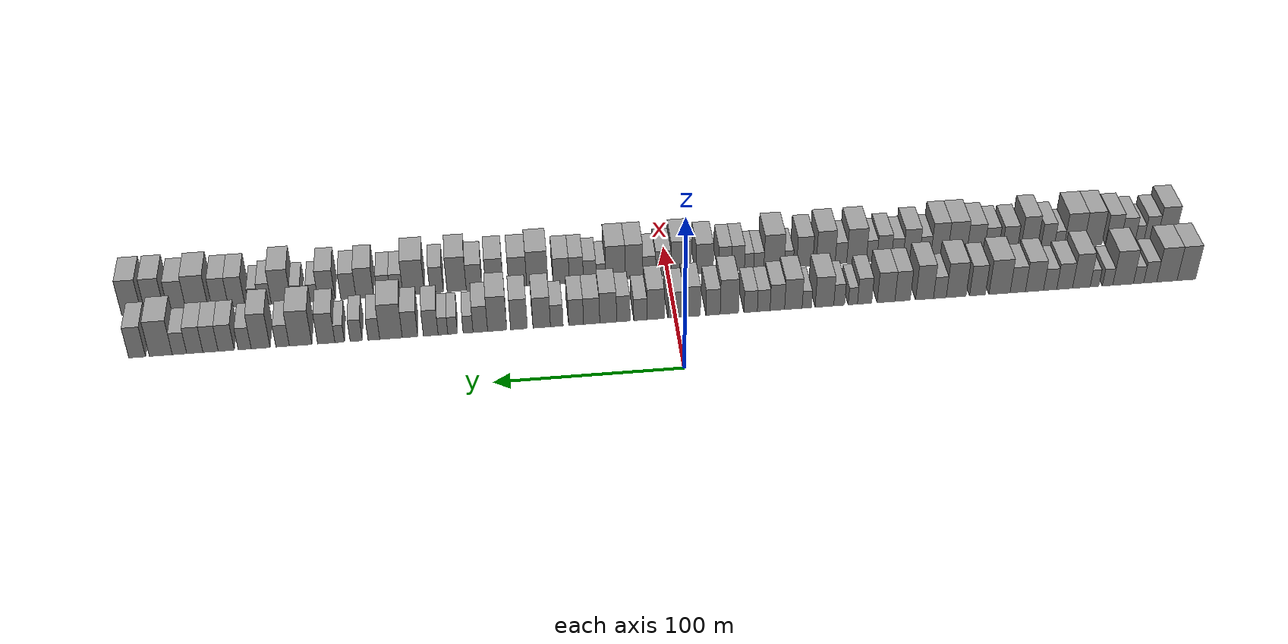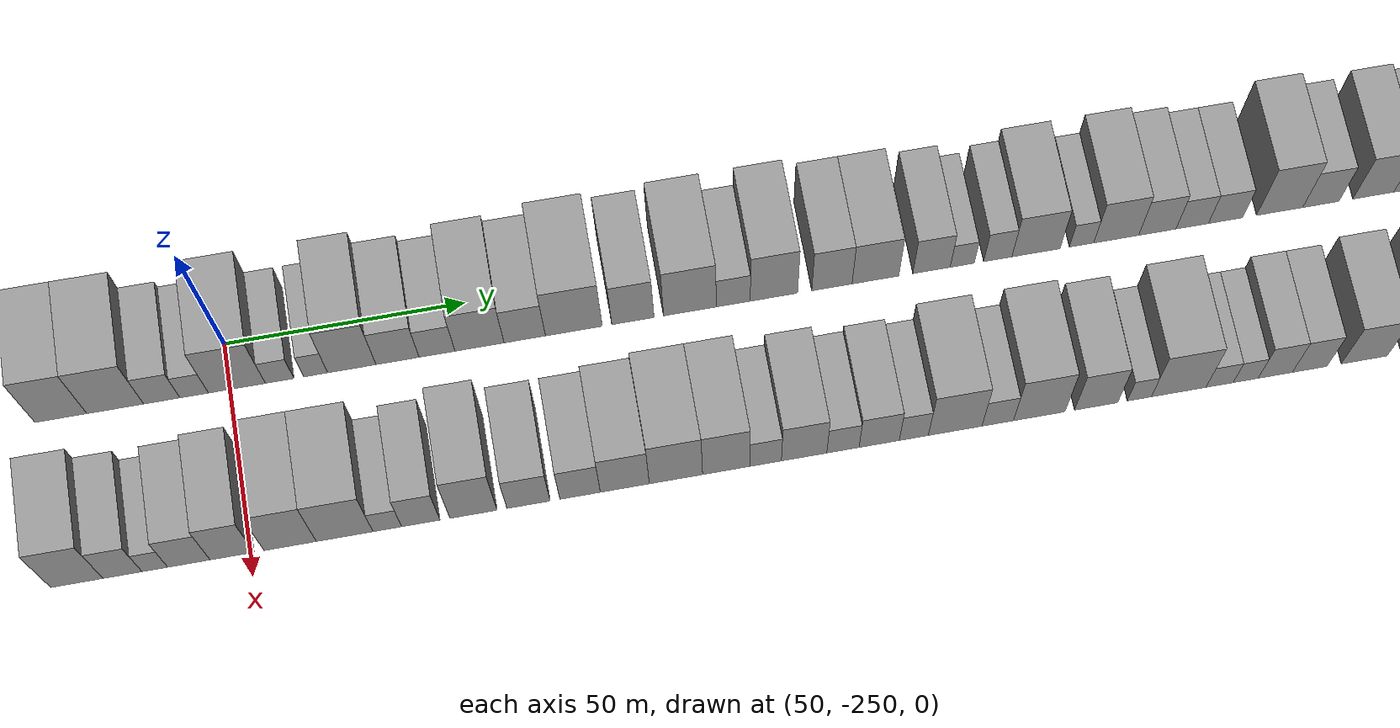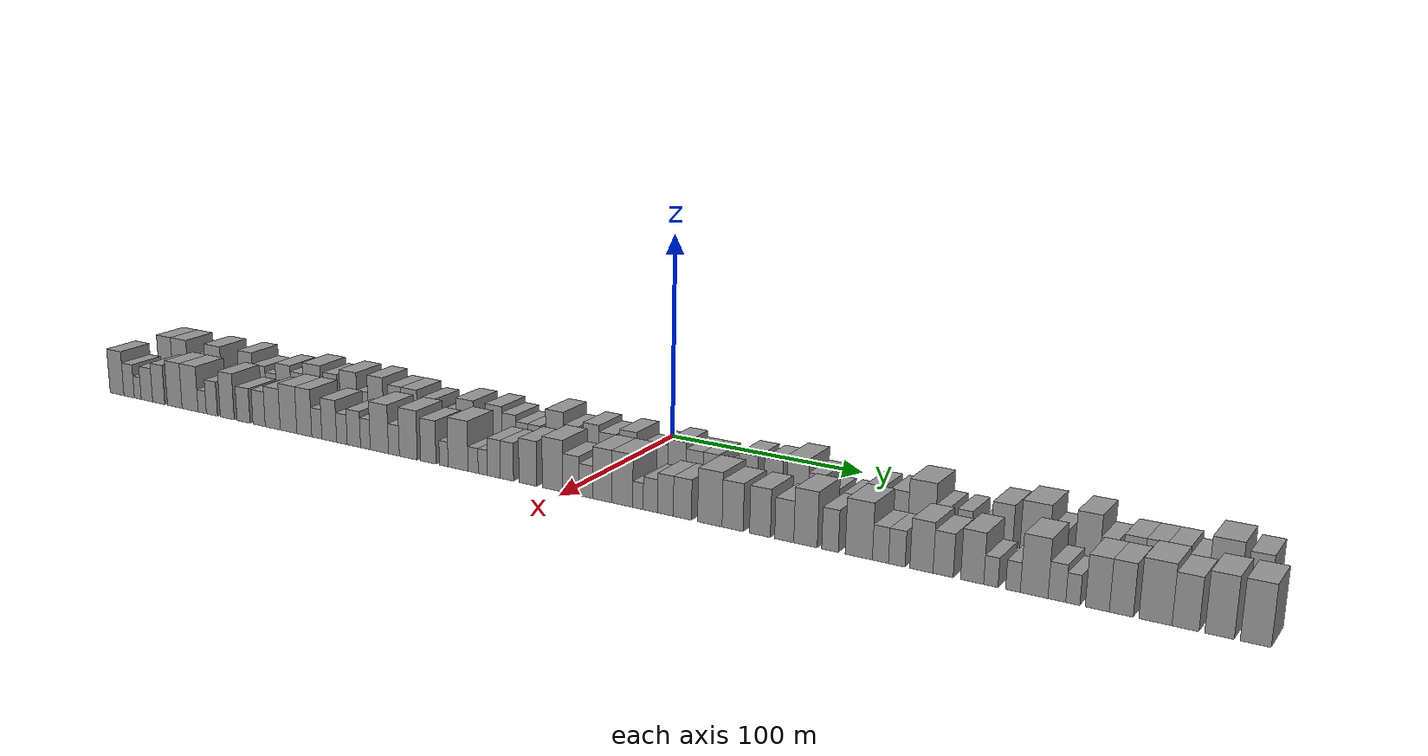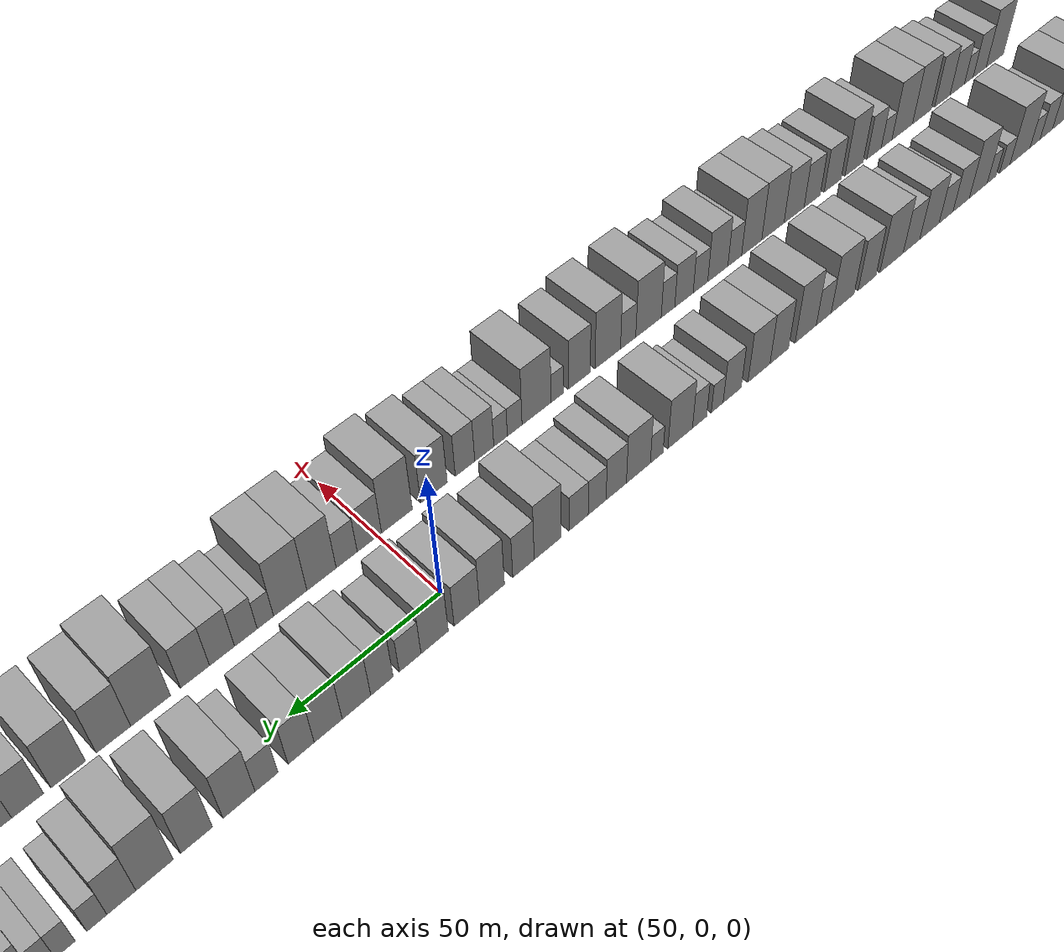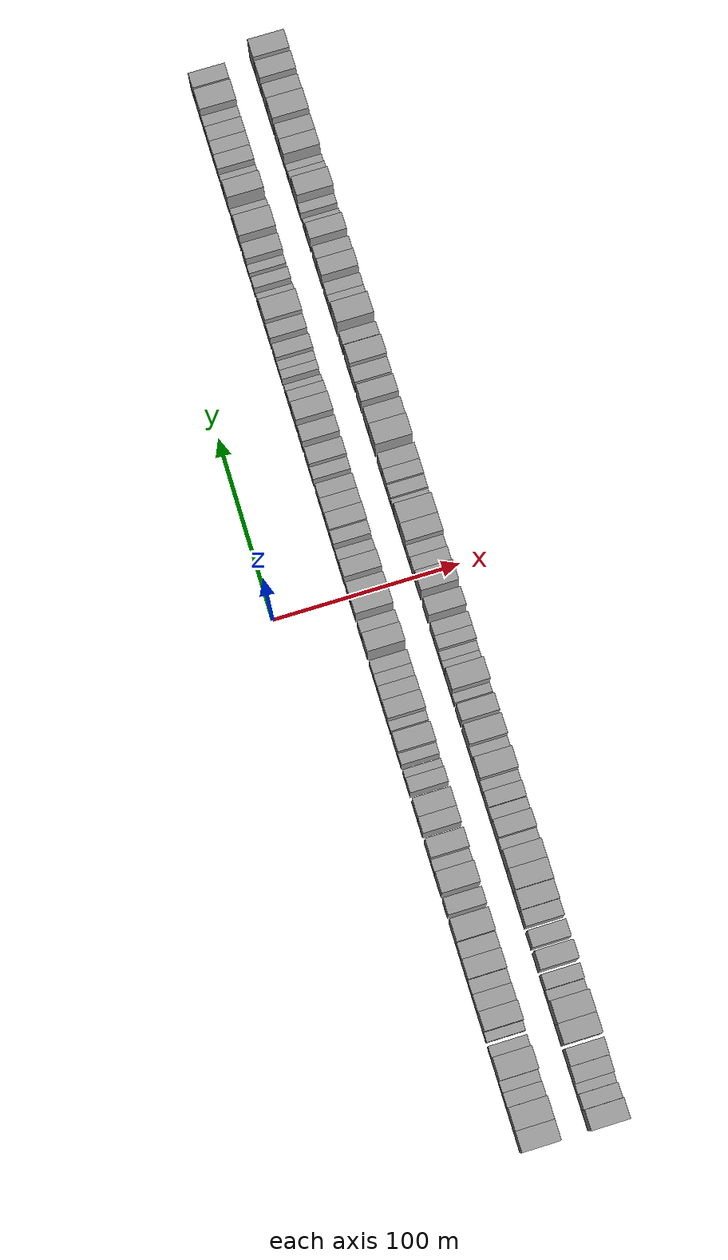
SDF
<sdf version="1.6">
 <world name="default">
  <scene>
   <sky><clouds><speed>12</speed></clouds></sky>
   <ambient>0.4 0.4 0.4 1</ambient>
   <background>0.7 0.7 0.7 1</background>
   <shadows>1</shadows>
  </scene>
  <gravity>0 0 -9.8066</gravity>
  <magnetic_field>6e-06 2.3e-05 -4.2e-05</magnetic_field>
  <physics default="0" name="default_physics" type="ode">
   <ode>
    <solver>
     <type>quick</type>
     <iters>10</iters>
     <sor>1.0</sor>
     <use_dynamic_moi_rescaling>0</use_dynamic_moi_rescaling>
    </solver>
    <constraints>
     <cfm>0</cfm>
     <erp>0.2</erp>
     <contact_max_correcting_vel>100</contact_max_correcting_vel>
     <contact_surface_layer>0.001</contact_surface_layer>
    </constraints>
   </ode>
   <max_step_size>0.004</max_step_size>
   <real_time_factor>1</real_time_factor>
   <real_time_update_rate>250</real_time_update_rate>
  </physics>
  <light name="sun" type="directional">
   <pose>0 0 10 0 0 0</pose>
   <diffuse>0.8 0.8 0.8 1</diffuse>
   <specular>0.2 0.2 0.2 1</specular>
   <attenuation>
    <range>1000</range>
    <constant>0.9</constant>
    <linear>0.01</linear>
    <quadratic>0.001</quadratic>
   </attenuation>
   <direction>-0.5 0.1 -0.9</direction>
  </light>
  <model name="building_1">
   <static>1</static>
   <pose>50.0000 -284.7026 0 0.000000 0.000000 0.000000</pose>
   <link name="link">
    <pose>0 0 12.00 0 0 0</pose>
    <collision name="collision"><geometry><box><size>20.0000 10.5947 24.0000</size></box></geometry></collision>
    <visual name="visual">
     <cast_shadows>0</cast_shadows>
     <geometry><box><size>20.0000 10.5947 24.0000</size></box></geometry>
     <material>
      <script>
       <uri>model://grey_wall/materials/scripts</uri>
       <uri>model://grey_wall/materials/textures</uri>
       <name>vrc/grey_wall</name>
      </script>
     </material>
    </visual>
   </link>
  </model>
  <model name="building_2">
   <static>1</static>
   <pose>50.0000 -273.5966 0 0.000000 0.000000 0.000000</pose>
   <link name="link">
    <pose>0 0 12.00 0 0 0</pose>
    <collision name="collision"><geometry><box><size>20.0000 11.6172 24.0000</size></box></geometry></collision>
    <visual name="visual">
     <cast_shadows>0</cast_shadows>
     <geometry><box><size>20.0000 11.6172 24.0000</size></box></geometry>
     <material>
      <script>
       <uri>model://grey_wall/materials/scripts</uri>
       <uri>model://grey_wall/materials/textures</uri>
       <name>vrc/grey_wall</name>
      </script>
     </material>
    </visual>
   </link>
  </model>
  <model name="building_3">
   <static>1</static>
   <pose>50.0000 -264.0849 0 0.000000 0.000000 0.000000</pose>
   <link name="link">
    <pose>0 0 7.50 0 0 0</pose>
    <collision name="collision"><geometry><box><size>20.0000 7.4063 15.0000</size></box></geometry></collision>
    <visual name="visual">
     <cast_shadows>0</cast_shadows>
     <geometry><box><size>20.0000 7.4063 15.0000</size></box></geometry>
     <material>
      <script>
       <uri>model://grey_wall/materials/scripts</uri>
       <uri>model://grey_wall/materials/textures</uri>
       <name>vrc/grey_wall</name>
      </script>
     </material>
    </visual>
   </link>
  </model>
  <model name="building_4">
   <static>1</static>
   <pose>50.0000 -257.4461 0 0.000000 0.000000 0.000000</pose>
   <link name="link">
    <pose>0 0 6.00 0 0 0</pose>
    <collision name="collision"><geometry><box><size>20.0000 5.8713 12.0000</size></box></geometry></collision>
    <visual name="visual">
     <cast_shadows>0</cast_shadows>
     <geometry><box><size>20.0000 5.8713 12.0000</size></box></geometry>
     <material>
      <script>
       <uri>model://grey_wall/materials/scripts</uri>
       <uri>model://grey_wall/materials/textures</uri>
       <name>vrc/grey_wall</name>
      </script>
     </material>
    </visual>
   </link>
  </model>
  <model name="building_5">
   <static>1</static>
   <pose>50.0000 -248.6617 0 0.000000 0.000000 0.000000</pose>
   <link name="link">
    <pose>0 0 12.00 0 0 0</pose>
    <collision name="collision"><geometry><box><size>20.0000 11.6974 24.0000</size></box></geometry></collision>
    <visual name="visual">
     <cast_shadows>0</cast_shadows>
     <geometry><box><size>20.0000 11.6974 24.0000</size></box></geometry>
     <material>
      <script>
       <uri>model://grey_wall/materials/scripts</uri>
       <uri>model://grey_wall/materials/textures</uri>
       <name>vrc/grey_wall</name>
      </script>
     </material>
    </visual>
   </link>
  </model>
  <model name="building_6">
   <static>1</static>
   <pose>50.0000 -239.8674 0 0.000000 0.000000 0.000000</pose>
   <link name="link">
    <pose>0 0 6.00 0 0 0</pose>
    <collision name="collision"><geometry><box><size>20.0000 5.8914 12.0000</size></box></geometry></collision>
    <visual name="visual">
     <cast_shadows>0</cast_shadows>
     <geometry><box><size>20.0000 5.8914 12.0000</size></box></geometry>
     <material>
      <script>
       <uri>model://grey_wall/materials/scripts</uri>
       <uri>model://grey_wall/materials/textures</uri>
       <name>vrc/grey_wall</name>
      </script>
     </material>
    </visual>
   </link>
  </model>
  <model name="building_7">
   <static>1</static>
   <pose>50.0000 -232.4474 0 0.000000 0.000000 0.000000</pose>
   <link name="link">
    <pose>0 0 6.00 0 0 0</pose>
    <collision name="collision"><geometry><box><size>20.0000 4.9485 12.0000</size></box></geometry></collision>
    <visual name="visual">
     <cast_shadows>0</cast_shadows>
     <geometry><box><size>20.0000 4.9485 12.0000</size></box></geometry>
     <material>
      <script>
       <uri>model://grey_wall/materials/scripts</uri>
       <uri>model://grey_wall/materials/textures</uri>
       <name>vrc/grey_wall</name>
      </script>
     </material>
    </visual>
   </link>
  </model>
  <model name="building_8">
   <static>1</static>
   <pose>50.0000 -224.9844 0 0.000000 0.000000 0.000000</pose>
   <link name="link">
    <pose>0 0 12.00 0 0 0</pose>
    <collision name="collision"><geometry><box><size>20.0000 9.9776 24.0000</size></box></geometry></collision>
    <visual name="visual">
     <cast_shadows>0</cast_shadows>
     <geometry><box><size>20.0000 9.9776 24.0000</size></box></geometry>
     <material>
      <script>
       <uri>model://grey_wall/materials/scripts</uri>
       <uri>model://grey_wall/materials/textures</uri>
       <name>vrc/grey_wall</name>
      </script>
     </material>
    </visual>
   </link>
  </model>
  <model name="building_9">
   <static>1</static>
   <pose>50.0000 -215.5335 0 0.000000 0.000000 0.000000</pose>
   <link name="link">
    <pose>0 0 9.00 0 0 0</pose>
    <collision name="collision"><geometry><box><size>20.0000 8.9242 18.0000</size></box></geometry></collision>
    <visual name="visual">
     <cast_shadows>0</cast_shadows>
     <geometry><box><size>20.0000 8.9242 18.0000</size></box></geometry>
     <material>
      <script>
       <uri>model://grey_wall/materials/scripts</uri>
       <uri>model://grey_wall/materials/textures</uri>
       <name>vrc/grey_wall</name>
      </script>
     </material>
    </visual>
   </link>
  </model>
  <model name="building_10">
   <static>1</static>
   <pose>50.0000 -207.3426 0 0.000000 0.000000 0.000000</pose>
   <link name="link">
    <pose>0 0 7.50 0 0 0</pose>
    <collision name="collision"><geometry><box><size>20.0000 7.4575 15.0000</size></box></geometry></collision>
    <visual name="visual">
     <cast_shadows>0</cast_shadows>
     <geometry><box><size>20.0000 7.4575 15.0000</size></box></geometry>
     <material>
      <script>
       <uri>model://grey_wall/materials/scripts</uri>
       <uri>model://grey_wall/materials/textures</uri>
       <name>vrc/grey_wall</name>
      </script>
     </material>
    </visual>
   </link>
  </model>
  <model name="building_11">
   <static>1</static>
   <pose>50.0000 -198.5121 0 0.000000 0.000000 0.000000</pose>
   <link name="link">
    <pose>0 0 10.50 0 0 0</pose>
    <collision name="collision"><geometry><box><size>20.0000 10.2037 21.0000</size></box></geometry></collision>
    <visual name="visual">
     <cast_shadows>0</cast_shadows>
     <geometry><box><size>20.0000 10.2037 21.0000</size></box></geometry>
     <material>
      <script>
       <uri>model://grey_wall/materials/scripts</uri>
       <uri>model://grey_wall/materials/textures</uri>
       <name>vrc/grey_wall</name>
      </script>
     </material>
    </visual>
   </link>
  </model>
  <model name="building_12">
   <static>1</static>
   <pose>50.0000 -189.1027 0 0.000000 0.000000 0.000000</pose>
   <link name="link">
    <pose>0 0 9.00 0 0 0</pose>
    <collision name="collision"><geometry><box><size>20.0000 8.6149 18.0000</size></box></geometry></collision>
    <visual name="visual">
     <cast_shadows>0</cast_shadows>
     <geometry><box><size>20.0000 8.6149 18.0000</size></box></geometry>
     <material>
      <script>
       <uri>model://grey_wall/materials/scripts</uri>
       <uri>model://grey_wall/materials/textures</uri>
       <name>vrc/grey_wall</name>
      </script>
     </material>
    </visual>
   </link>
  </model>
  <model name="building_13">
   <static>1</static>
   <pose>50.0000 -178.8727 0 0.000000 0.000000 0.000000</pose>
   <link name="link">
    <pose>0 0 12.00 0 0 0</pose>
    <collision name="collision"><geometry><box><size>20.0000 11.8451 24.0000</size></box></geometry></collision>
    <visual name="visual">
     <cast_shadows>0</cast_shadows>
     <geometry><box><size>20.0000 11.8451 24.0000</size></box></geometry>
     <material>
      <script>
       <uri>model://grey_wall/materials/scripts</uri>
       <uri>model://grey_wall/materials/textures</uri>
       <name>vrc/grey_wall</name>
      </script>
     </material>
    </visual>
   </link>
  </model>
  <model name="building_14">
   <static>1</static>
   <pose>50.0000 -166.5378 0 0.000000 0.000000 0.000000</pose>
   <link name="link">
    <pose>0 0 10.50 0 0 0</pose>
    <collision name="collision"><geometry><box><size>20.0000 8.8249 21.0000</size></box></geometry></collision>
    <visual name="visual">
     <cast_shadows>0</cast_shadows>
     <geometry><box><size>20.0000 8.8249 21.0000</size></box></geometry>
     <material>
      <script>
       <uri>model://grey_wall/materials/scripts</uri>
       <uri>model://grey_wall/materials/textures</uri>
       <name>vrc/grey_wall</name>
      </script>
     </material>
    </visual>
   </link>
  </model>
  <model name="building_15">
   <static>1</static>
   <pose>50.0000 -154.5810 0 0.000000 0.000000 0.000000</pose>
   <link name="link">
    <pose>0 0 12.00 0 0 0</pose>
    <collision name="collision"><geometry><box><size>20.0000 11.0885 24.0000</size></box></geometry></collision>
    <visual name="visual">
     <cast_shadows>0</cast_shadows>
     <geometry><box><size>20.0000 11.0885 24.0000</size></box></geometry>
     <material>
      <script>
       <uri>model://grey_wall/materials/scripts</uri>
       <uri>model://grey_wall/materials/textures</uri>
       <name>vrc/grey_wall</name>
      </script>
     </material>
    </visual>
   </link>
  </model>
  <model name="building_16">
   <static>1</static>
   <pose>50.0000 -145.4833 0 0.000000 0.000000 0.000000</pose>
   <link name="link">
    <pose>0 0 7.50 0 0 0</pose>
    <collision name="collision"><geometry><box><size>20.0000 7.1070 15.0000</size></box></geometry></collision>
    <visual name="visual">
     <cast_shadows>0</cast_shadows>
     <geometry><box><size>20.0000 7.1070 15.0000</size></box></geometry>
     <material>
      <script>
       <uri>model://grey_wall/materials/scripts</uri>
       <uri>model://grey_wall/materials/textures</uri>
       <name>vrc/grey_wall</name>
      </script>
     </material>
    </visual>
   </link>
  </model>
  <model name="building_17">
   <static>1</static>
   <pose>50.0000 -136.9539 0 0.000000 0.000000 0.000000</pose>
   <link name="link">
    <pose>0 0 12.00 0 0 0</pose>
    <collision name="collision"><geometry><box><size>20.0000 9.9518 24.0000</size></box></geometry></collision>
    <visual name="visual">
     <cast_shadows>0</cast_shadows>
     <geometry><box><size>20.0000 9.9518 24.0000</size></box></geometry>
     <material>
      <script>
       <uri>model://grey_wall/materials/scripts</uri>
       <uri>model://grey_wall/materials/textures</uri>
       <name>vrc/grey_wall</name>
      </script>
     </material>
    </visual>
   </link>
  </model>
  <model name="building_18">
   <static>1</static>
   <pose>50.0000 -124.7235 0 0.000000 0.000000 0.000000</pose>
   <link name="link">
    <pose>0 0 10.50 0 0 0</pose>
    <collision name="collision"><geometry><box><size>20.0000 8.5091 21.0000</size></box></geometry></collision>
    <visual name="visual">
     <cast_shadows>0</cast_shadows>
     <geometry><box><size>20.0000 8.5091 21.0000</size></box></geometry>
     <material>
      <script>
       <uri>model://grey_wall/materials/scripts</uri>
       <uri>model://grey_wall/materials/textures</uri>
       <name>vrc/grey_wall</name>
      </script>
     </material>
    </visual>
   </link>
  </model>
  <model name="building_19">
   <static>1</static>
   <pose>50.0000 -115.5313 0 0.000000 0.000000 0.000000</pose>
   <link name="link">
    <pose>0 0 10.50 0 0 0</pose>
    <collision name="collision"><geometry><box><size>20.0000 9.8753 21.0000</size></box></geometry></collision>
    <visual name="visual">
     <cast_shadows>0</cast_shadows>
     <geometry><box><size>20.0000 9.8753 21.0000</size></box></geometry>
     <material>
      <script>
       <uri>model://grey_wall/materials/scripts</uri>
       <uri>model://grey_wall/materials/textures</uri>
       <name>vrc/grey_wall</name>
      </script>
     </material>
    </visual>
   </link>
  </model>
  <model name="building_20">
   <static>1</static>
   <pose>50.0000 -103.6340 0 0.000000 0.000000 0.000000</pose>
   <link name="link">
    <pose>0 0 9.00 0 0 0</pose>
    <collision name="collision"><geometry><box><size>20.0000 7.9193 18.0000</size></box></geometry></collision>
    <visual name="visual">
     <cast_shadows>0</cast_shadows>
     <geometry><box><size>20.0000 7.9193 18.0000</size></box></geometry>
     <material>
      <script>
       <uri>model://grey_wall/materials/scripts</uri>
       <uri>model://grey_wall/materials/textures</uri>
       <name>vrc/grey_wall</name>
      </script>
     </material>
    </visual>
   </link>
  </model>
  <model name="building_21">
   <static>1</static>
   <pose>50.0000 -97.1221 0 0.000000 0.000000 0.000000</pose>
   <link name="link">
    <pose>0 0 6.00 0 0 0</pose>
    <collision name="collision"><geometry><box><size>20.0000 5.1045 12.0000</size></box></geometry></collision>
    <visual name="visual">
     <cast_shadows>0</cast_shadows>
     <geometry><box><size>20.0000 5.1045 12.0000</size></box></geometry>
     <material>
      <script>
       <uri>model://grey_wall/materials/scripts</uri>
       <uri>model://grey_wall/materials/textures</uri>
       <name>vrc/grey_wall</name>
      </script>
     </material>
    </visual>
   </link>
  </model>
  <model name="building_22">
   <static>1</static>
   <pose>50.0000 -89.5682 0 0.000000 0.000000 0.000000</pose>
   <link name="link">
    <pose>0 0 7.50 0 0 0</pose>
    <collision name="collision"><geometry><box><size>20.0000 6.0033 15.0000</size></box></geometry></collision>
    <visual name="visual">
     <cast_shadows>0</cast_shadows>
     <geometry><box><size>20.0000 6.0033 15.0000</size></box></geometry>
     <material>
      <script>
       <uri>model://grey_wall/materials/scripts</uri>
       <uri>model://grey_wall/materials/textures</uri>
       <name>vrc/grey_wall</name>
      </script>
     </material>
    </visual>
   </link>
  </model>
  <model name="building_23">
   <static>1</static>
   <pose>50.0000 -81.4354 0 0.000000 0.000000 0.000000</pose>
   <link name="link">
    <pose>0 0 10.50 0 0 0</pose>
    <collision name="collision"><geometry><box><size>20.0000 10.2623 21.0000</size></box></geometry></collision>
    <visual name="visual">
     <cast_shadows>0</cast_shadows>
     <geometry><box><size>20.0000 10.2623 21.0000</size></box></geometry>
     <material>
      <script>
       <uri>model://grey_wall/materials/scripts</uri>
       <uri>model://grey_wall/materials/textures</uri>
       <name>vrc/grey_wall</name>
      </script>
     </material>
    </visual>
   </link>
  </model>
  <model name="building_24">
   <static>1</static>
   <pose>50.0000 -71.7122 0 0.000000 0.000000 0.000000</pose>
   <link name="link">
    <pose>0 0 6.00 0 0 0</pose>
    <collision name="collision"><geometry><box><size>20.0000 5.1841 12.0000</size></box></geometry></collision>
    <visual name="visual">
     <cast_shadows>0</cast_shadows>
     <geometry><box><size>20.0000 5.1841 12.0000</size></box></geometry>
     <material>
      <script>
       <uri>model://grey_wall/materials/scripts</uri>
       <uri>model://grey_wall/materials/textures</uri>
       <name>vrc/grey_wall</name>
      </script>
     </material>
    </visual>
   </link>
  </model>
  <model name="building_25">
   <static>1</static>
   <pose>50.0000 -64.2973 0 0.000000 0.000000 0.000000</pose>
   <link name="link">
    <pose>0 0 10.50 0 0 0</pose>
    <collision name="collision"><geometry><box><size>20.0000 9.6455 21.0000</size></box></geometry></collision>
    <visual name="visual">
     <cast_shadows>0</cast_shadows>
     <geometry><box><size>20.0000 9.6455 21.0000</size></box></geometry>
     <material>
      <script>
       <uri>model://grey_wall/materials/scripts</uri>
       <uri>model://grey_wall/materials/textures</uri>
       <name>vrc/grey_wall</name>
      </script>
     </material>
    </visual>
   </link>
  </model>
  <model name="building_26">
   <static>1</static>
   <pose>50.0000 -55.4743 0 0.000000 0.000000 0.000000</pose>
   <link name="link">
    <pose>0 0 9.00 0 0 0</pose>
    <collision name="collision"><geometry><box><size>20.0000 8.0005 18.0000</size></box></geometry></collision>
    <visual name="visual">
     <cast_shadows>0</cast_shadows>
     <geometry><box><size>20.0000 8.0005 18.0000</size></box></geometry>
     <material>
      <script>
       <uri>model://grey_wall/materials/scripts</uri>
       <uri>model://grey_wall/materials/textures</uri>
       <name>vrc/grey_wall</name>
      </script>
     </material>
    </visual>
   </link>
  </model>
  <model name="building_27">
   <static>1</static>
   <pose>50.0000 -47.9953 0 0.000000 0.000000 0.000000</pose>
   <link name="link">
    <pose>0 0 7.50 0 0 0</pose>
    <collision name="collision"><geometry><box><size>20.0000 6.9575 15.0000</size></box></geometry></collision>
    <visual name="visual">
     <cast_shadows>0</cast_shadows>
     <geometry><box><size>20.0000 6.9575 15.0000</size></box></geometry>
     <material>
      <script>
       <uri>model://grey_wall/materials/scripts</uri>
       <uri>model://grey_wall/materials/textures</uri>
       <name>vrc/grey_wall</name>
      </script>
     </material>
    </visual>
   </link>
  </model>
  <model name="building_28">
   <static>1</static>
   <pose>50.0000 -40.8460 0 0.000000 0.000000 0.000000</pose>
   <link name="link">
    <pose>0 0 7.50 0 0 0</pose>
    <collision name="collision"><geometry><box><size>20.0000 7.3411 15.0000</size></box></geometry></collision>
    <visual name="visual">
     <cast_shadows>0</cast_shadows>
     <geometry><box><size>20.0000 7.3411 15.0000</size></box></geometry>
     <material>
      <script>
       <uri>model://grey_wall/materials/scripts</uri>
       <uri>model://grey_wall/materials/textures</uri>
       <name>vrc/grey_wall</name>
      </script>
     </material>
    </visual>
   </link>
  </model>
  <model name="building_29">
   <static>1</static>
   <pose>50.0000 -29.1868 0 0.000000 0.000000 0.000000</pose>
   <link name="link">
    <pose>0 0 12.00 0 0 0</pose>
    <collision name="collision"><geometry><box><size>20.0000 9.9773 24.0000</size></box></geometry></collision>
    <visual name="visual">
     <cast_shadows>0</cast_shadows>
     <geometry><box><size>20.0000 9.9773 24.0000</size></box></geometry>
     <material>
      <script>
       <uri>model://grey_wall/materials/scripts</uri>
       <uri>model://grey_wall/materials/textures</uri>
       <name>vrc/grey_wall</name>
      </script>
     </material>
    </visual>
   </link>
  </model>
  <model name="building_30">
   <static>1</static>
   <pose>50.0000 -20.2898 0 0.000000 0.000000 0.000000</pose>
   <link name="link">
    <pose>0 0 9.00 0 0 0</pose>
    <collision name="collision"><geometry><box><size>20.0000 7.8167 18.0000</size></box></geometry></collision>
    <visual name="visual">
     <cast_shadows>0</cast_shadows>
     <geometry><box><size>20.0000 7.8167 18.0000</size></box></geometry>
     <material>
      <script>
       <uri>model://grey_wall/materials/scripts</uri>
       <uri>model://grey_wall/materials/textures</uri>
       <name>vrc/grey_wall</name>
      </script>
     </material>
    </visual>
   </link>
  </model>
  <model name="building_31">
   <static>1</static>
   <pose>50.0000 -8.9502 0 0.000000 0.000000 0.000000</pose>
   <link name="link">
    <pose>0 0 10.50 0 0 0</pose>
    <collision name="collision"><geometry><box><size>20.0000 8.8623 21.0000</size></box></geometry></collision>
    <visual name="visual">
     <cast_shadows>0</cast_shadows>
     <geometry><box><size>20.0000 8.8623 21.0000</size></box></geometry>
     <material>
      <script>
       <uri>model://grey_wall/materials/scripts</uri>
       <uri>model://grey_wall/materials/textures</uri>
       <name>vrc/grey_wall</name>
      </script>
     </material>
    </visual>
   </link>
  </model>
  <model name="building_32">
   <static>1</static>
   <pose>50.0000 -0.1059 0 0.000000 0.000000 0.000000</pose>
   <link name="link">
    <pose>0 0 9.00 0 0 0</pose>
    <collision name="collision"><geometry><box><size>20.0000 8.8263 18.0000</size></box></geometry></collision>
    <visual name="visual">
     <cast_shadows>0</cast_shadows>
     <geometry><box><size>20.0000 8.8263 18.0000</size></box></geometry>
     <material>
      <script>
       <uri>model://grey_wall/materials/scripts</uri>
       <uri>model://grey_wall/materials/textures</uri>
       <name>vrc/grey_wall</name>
      </script>
     </material>
    </visual>
   </link>
  </model>
  <model name="building_33">
   <static>1</static>
   <pose>50.0000 10.9382 0 0.000000 0.000000 0.000000</pose>
   <link name="link">
    <pose>0 0 10.50 0 0 0</pose>
    <collision name="collision"><geometry><box><size>20.0000 9.2619 21.0000</size></box></geometry></collision>
    <visual name="visual">
     <cast_shadows>0</cast_shadows>
     <geometry><box><size>20.0000 9.2619 21.0000</size></box></geometry>
     <material>
      <script>
       <uri>model://grey_wall/materials/scripts</uri>
       <uri>model://grey_wall/materials/textures</uri>
       <name>vrc/grey_wall</name>
      </script>
     </material>
    </visual>
   </link>
  </model>
  <model name="building_34">
   <static>1</static>
   <pose>50.0000 19.1914 0 0.000000 0.000000 0.000000</pose>
   <link name="link">
    <pose>0 0 7.50 0 0 0</pose>
    <collision name="collision"><geometry><box><size>20.0000 7.2445 15.0000</size></box></geometry></collision>
    <visual name="visual">
     <cast_shadows>0</cast_shadows>
     <geometry><box><size>20.0000 7.2445 15.0000</size></box></geometry>
     <material>
      <script>
       <uri>model://grey_wall/materials/scripts</uri>
       <uri>model://grey_wall/materials/textures</uri>
       <name>vrc/grey_wall</name>
      </script>
     </material>
    </visual>
   </link>
  </model>
  <model name="building_35">
   <static>1</static>
   <pose>50.0000 28.4466 0 0.000000 0.000000 0.000000</pose>
   <link name="link">
    <pose>0 0 9.00 0 0 0</pose>
    <collision name="collision"><geometry><box><size>20.0000 7.2659 18.0000</size></box></geometry></collision>
    <visual name="visual">
     <cast_shadows>0</cast_shadows>
     <geometry><box><size>20.0000 7.2659 18.0000</size></box></geometry>
     <material>
      <script>
       <uri>model://grey_wall/materials/scripts</uri>
       <uri>model://grey_wall/materials/textures</uri>
       <name>vrc/grey_wall</name>
      </script>
     </material>
    </visual>
   </link>
  </model>
  <model name="building_36">
   <static>1</static>
   <pose>50.0000 36.6467 0 0.000000 0.000000 0.000000</pose>
   <link name="link">
    <pose>0 0 10.50 0 0 0</pose>
    <collision name="collision"><geometry><box><size>20.0000 9.1343 21.0000</size></box></geometry></collision>
    <visual name="visual">
     <cast_shadows>0</cast_shadows>
     <geometry><box><size>20.0000 9.1343 21.0000</size></box></geometry>
     <material>
      <script>
       <uri>model://grey_wall/materials/scripts</uri>
       <uri>model://grey_wall/materials/textures</uri>
       <name>vrc/grey_wall</name>
      </script>
     </material>
    </visual>
   </link>
  </model>
  <model name="building_37">
   <static>1</static>
   <pose>50.0000 45.5861 0 0.000000 0.000000 0.000000</pose>
   <link name="link">
    <pose>0 0 9.00 0 0 0</pose>
    <collision name="collision"><geometry><box><size>20.0000 8.7445 18.0000</size></box></geometry></collision>
    <visual name="visual">
     <cast_shadows>0</cast_shadows>
     <geometry><box><size>20.0000 8.7445 18.0000</size></box></geometry>
     <material>
      <script>
       <uri>model://grey_wall/materials/scripts</uri>
       <uri>model://grey_wall/materials/textures</uri>
       <name>vrc/grey_wall</name>
      </script>
     </material>
    </visual>
   </link>
  </model>
  <model name="building_38">
   <static>1</static>
   <pose>50.0000 53.9512 0 0.000000 0.000000 0.000000</pose>
   <link name="link">
    <pose>0 0 9.00 0 0 0</pose>
    <collision name="collision"><geometry><box><size>20.0000 7.9858 18.0000</size></box></geometry></collision>
    <visual name="visual">
     <cast_shadows>0</cast_shadows>
     <geometry><box><size>20.0000 7.9858 18.0000</size></box></geometry>
     <material>
      <script>
       <uri>model://grey_wall/materials/scripts</uri>
       <uri>model://grey_wall/materials/textures</uri>
       <name>vrc/grey_wall</name>
      </script>
     </material>
    </visual>
   </link>
  </model>
  <model name="building_39">
   <static>1</static>
   <pose>50.0000 64.3658 0 0.000000 0.000000 0.000000</pose>
   <link name="link">
    <pose>0 0 7.50 0 0 0</pose>
    <collision name="collision"><geometry><box><size>20.0000 6.8434 15.0000</size></box></geometry></collision>
    <visual name="visual">
     <cast_shadows>0</cast_shadows>
     <geometry><box><size>20.0000 6.8434 15.0000</size></box></geometry>
     <material>
      <script>
       <uri>model://grey_wall/materials/scripts</uri>
       <uri>model://grey_wall/materials/textures</uri>
       <name>vrc/grey_wall</name>
      </script>
     </material>
    </visual>
   </link>
  </model>
  <model name="building_40">
   <static>1</static>
   <pose>50.0000 72.4730 0 0.000000 0.000000 0.000000</pose>
   <link name="link">
    <pose>0 0 10.50 0 0 0</pose>
    <collision name="collision"><geometry><box><size>20.0000 9.3710 21.0000</size></box></geometry></collision>
    <visual name="visual">
     <cast_shadows>0</cast_shadows>
     <geometry><box><size>20.0000 9.3710 21.0000</size></box></geometry>
     <material>
      <script>
       <uri>model://grey_wall/materials/scripts</uri>
       <uri>model://grey_wall/materials/textures</uri>
       <name>vrc/grey_wall</name>
      </script>
     </material>
    </visual>
   </link>
  </model>
  <model name="building_41">
   <static>1</static>
   <pose>50.0000 84.6724 0 0.000000 0.000000 0.000000</pose>
   <link name="link">
    <pose>0 0 10.50 0 0 0</pose>
    <collision name="collision"><geometry><box><size>20.0000 9.0277 21.0000</size></box></geometry></collision>
    <visual name="visual">
     <cast_shadows>0</cast_shadows>
     <geometry><box><size>20.0000 9.0277 21.0000</size></box></geometry>
     <material>
      <script>
       <uri>model://grey_wall/materials/scripts</uri>
       <uri>model://grey_wall/materials/textures</uri>
       <name>vrc/grey_wall</name>
      </script>
     </material>
    </visual>
   </link>
  </model>
  <model name="building_42">
   <static>1</static>
   <pose>50.0000 96.3206 0 0.000000 0.000000 0.000000</pose>
   <link name="link">
    <pose>0 0 12.00 0 0 0</pose>
    <collision name="collision"><geometry><box><size>20.0000 10.2688 24.0000</size></box></geometry></collision>
    <visual name="visual">
     <cast_shadows>0</cast_shadows>
     <geometry><box><size>20.0000 10.2688 24.0000</size></box></geometry>
     <material>
      <script>
       <uri>model://grey_wall/materials/scripts</uri>
       <uri>model://grey_wall/materials/textures</uri>
       <name>vrc/grey_wall</name>
      </script>
     </material>
    </visual>
   </link>
  </model>
  <model name="building_43">
   <static>1</static>
   <pose>50.0000 105.3355 0 0.000000 0.000000 0.000000</pose>
   <link name="link">
    <pose>0 0 9.00 0 0 0</pose>
    <collision name="collision"><geometry><box><size>20.0000 7.7611 18.0000</size></box></geometry></collision>
    <visual name="visual">
     <cast_shadows>0</cast_shadows>
     <geometry><box><size>20.0000 7.7611 18.0000</size></box></geometry>
     <material>
      <script>
       <uri>model://grey_wall/materials/scripts</uri>
       <uri>model://grey_wall/materials/textures</uri>
       <name>vrc/grey_wall</name>
      </script>
     </material>
    </visual>
   </link>
  </model>
  <model name="building_44">
   <static>1</static>
   <pose>50.0000 111.8671 0 0.000000 0.000000 0.000000</pose>
   <link name="link">
    <pose>0 0 6.00 0 0 0</pose>
    <collision name="collision"><geometry><box><size>20.0000 5.3020 12.0000</size></box></geometry></collision>
    <visual name="visual">
     <cast_shadows>0</cast_shadows>
     <geometry><box><size>20.0000 5.3020 12.0000</size></box></geometry>
     <material>
      <script>
       <uri>model://grey_wall/materials/scripts</uri>
       <uri>model://grey_wall/materials/textures</uri>
       <name>vrc/grey_wall</name>
      </script>
     </material>
    </visual>
   </link>
  </model>
  <model name="building_45">
   <static>1</static>
   <pose>50.0000 120.0955 0 0.000000 0.000000 0.000000</pose>
   <link name="link">
    <pose>0 0 6.00 0 0 0</pose>
    <collision name="collision"><geometry><box><size>20.0000 5.1548 12.0000</size></box></geometry></collision>
    <visual name="visual">
     <cast_shadows>0</cast_shadows>
     <geometry><box><size>20.0000 5.1548 12.0000</size></box></geometry>
     <material>
      <script>
       <uri>model://grey_wall/materials/scripts</uri>
       <uri>model://grey_wall/materials/textures</uri>
       <name>vrc/grey_wall</name>
      </script>
     </material>
    </visual>
   </link>
  </model>
  <model name="building_46">
   <static>1</static>
   <pose>50.0000 125.2434 0 0.000000 0.000000 0.000000</pose>
   <link name="link">
    <pose>0 0 6.00 0 0 0</pose>
    <collision name="collision"><geometry><box><size>20.0000 5.1410 12.0000</size></box></geometry></collision>
    <visual name="visual">
     <cast_shadows>0</cast_shadows>
     <geometry><box><size>20.0000 5.1410 12.0000</size></box></geometry>
     <material>
      <script>
       <uri>model://grey_wall/materials/scripts</uri>
       <uri>model://grey_wall/materials/textures</uri>
       <name>vrc/grey_wall</name>
      </script>
     </material>
    </visual>
   </link>
  </model>
  <model name="building_47">
   <static>1</static>
   <pose>50.0000 131.7427 0 0.000000 0.000000 0.000000</pose>
   <link name="link">
    <pose>0 0 9.00 0 0 0</pose>
    <collision name="collision"><geometry><box><size>20.0000 7.8575 18.0000</size></box></geometry></collision>
    <visual name="visual">
     <cast_shadows>0</cast_shadows>
     <geometry><box><size>20.0000 7.8575 18.0000</size></box></geometry>
     <material>
      <script>
       <uri>model://grey_wall/materials/scripts</uri>
       <uri>model://grey_wall/materials/textures</uri>
       <name>vrc/grey_wall</name>
      </script>
     </material>
    </visual>
   </link>
  </model>
  <model name="building_48">
   <static>1</static>
   <pose>50.0000 142.7689 0 0.000000 0.000000 0.000000</pose>
   <link name="link">
    <pose>0 0 9.00 0 0 0</pose>
    <collision name="collision"><geometry><box><size>20.0000 8.1947 18.0000</size></box></geometry></collision>
    <visual name="visual">
     <cast_shadows>0</cast_shadows>
     <geometry><box><size>20.0000 8.1947 18.0000</size></box></geometry>
     <material>
      <script>
       <uri>model://grey_wall/materials/scripts</uri>
       <uri>model://grey_wall/materials/textures</uri>
       <name>vrc/grey_wall</name>
      </script>
     </material>
    </visual>
   </link>
  </model>
  <model name="building_49">
   <static>1</static>
   <pose>50.0000 152.8509 0 0.000000 0.000000 0.000000</pose>
   <link name="link">
    <pose>0 0 12.00 0 0 0</pose>
    <collision name="collision"><geometry><box><size>20.0000 11.9694 24.0000</size></box></geometry></collision>
    <visual name="visual">
     <cast_shadows>0</cast_shadows>
     <geometry><box><size>20.0000 11.9694 24.0000</size></box></geometry>
     <material>
      <script>
       <uri>model://grey_wall/materials/scripts</uri>
       <uri>model://grey_wall/materials/textures</uri>
       <name>vrc/grey_wall</name>
      </script>
     </material>
    </visual>
   </link>
  </model>
  <model name="building_50">
   <static>1</static>
   <pose>50.0000 161.9221 0 0.000000 0.000000 0.000000</pose>
   <link name="link">
    <pose>0 0 7.50 0 0 0</pose>
    <collision name="collision"><geometry><box><size>20.0000 6.1730 15.0000</size></box></geometry></collision>
    <visual name="visual">
     <cast_shadows>0</cast_shadows>
     <geometry><box><size>20.0000 6.1730 15.0000</size></box></geometry>
     <material>
      <script>
       <uri>model://grey_wall/materials/scripts</uri>
       <uri>model://grey_wall/materials/textures</uri>
       <name>vrc/grey_wall</name>
      </script>
     </material>
    </visual>
   </link>
  </model>
  <model name="building_51">
   <static>1</static>
   <pose>50.0000 171.2372 0 0.000000 0.000000 0.000000</pose>
   <link name="link">
    <pose>0 0 7.50 0 0 0</pose>
    <collision name="collision"><geometry><box><size>20.0000 6.4571 15.0000</size></box></geometry></collision>
    <visual name="visual">
     <cast_shadows>0</cast_shadows>
     <geometry><box><size>20.0000 6.4571 15.0000</size></box></geometry>
     <material>
      <script>
       <uri>model://grey_wall/materials/scripts</uri>
       <uri>model://grey_wall/materials/textures</uri>
       <name>vrc/grey_wall</name>
      </script>
     </material>
    </visual>
   </link>
  </model>
  <model name="building_52">
   <static>1</static>
   <pose>50.0000 179.9599 0 0.000000 0.000000 0.000000</pose>
   <link name="link">
    <pose>0 0 6.00 0 0 0</pose>
    <collision name="collision"><geometry><box><size>20.0000 4.9883 12.0000</size></box></geometry></collision>
    <visual name="visual">
     <cast_shadows>0</cast_shadows>
     <geometry><box><size>20.0000 4.9883 12.0000</size></box></geometry>
     <material>
      <script>
       <uri>model://grey_wall/materials/scripts</uri>
       <uri>model://grey_wall/materials/textures</uri>
       <name>vrc/grey_wall</name>
      </script>
     </material>
    </visual>
   </link>
  </model>
  <model name="building_53">
   <static>1</static>
   <pose>50.0000 187.0198 0 0.000000 0.000000 0.000000</pose>
   <link name="link">
    <pose>0 0 10.50 0 0 0</pose>
    <collision name="collision"><geometry><box><size>20.0000 9.1315 21.0000</size></box></geometry></collision>
    <visual name="visual">
     <cast_shadows>0</cast_shadows>
     <geometry><box><size>20.0000 9.1315 21.0000</size></box></geometry>
     <material>
      <script>
       <uri>model://grey_wall/materials/scripts</uri>
       <uri>model://grey_wall/materials/textures</uri>
       <name>vrc/grey_wall</name>
      </script>
     </material>
    </visual>
   </link>
  </model>
  <model name="building_54">
   <static>1</static>
   <pose>50.0000 200.5181 0 0.000000 0.000000 0.000000</pose>
   <link name="link">
    <pose>0 0 12.00 0 0 0</pose>
    <collision name="collision"><geometry><box><size>20.0000 11.8651 24.0000</size></box></geometry></collision>
    <visual name="visual">
     <cast_shadows>0</cast_shadows>
     <geometry><box><size>20.0000 11.8651 24.0000</size></box></geometry>
     <material>
      <script>
       <uri>model://grey_wall/materials/scripts</uri>
       <uri>model://grey_wall/materials/textures</uri>
       <name>vrc/grey_wall</name>
      </script>
     </material>
    </visual>
   </link>
  </model>
  <model name="building_55">
   <static>1</static>
   <pose>50.0000 209.9860 0 0.000000 0.000000 0.000000</pose>
   <link name="link">
    <pose>0 0 7.50 0 0 0</pose>
    <collision name="collision"><geometry><box><size>20.0000 7.0707 15.0000</size></box></geometry></collision>
    <visual name="visual">
     <cast_shadows>0</cast_shadows>
     <geometry><box><size>20.0000 7.0707 15.0000</size></box></geometry>
     <material>
      <script>
       <uri>model://grey_wall/materials/scripts</uri>
       <uri>model://grey_wall/materials/textures</uri>
       <name>vrc/grey_wall</name>
      </script>
     </material>
    </visual>
   </link>
  </model>
  <model name="building_56">
   <static>1</static>
   <pose>50.0000 221.4651 0 0.000000 0.000000 0.000000</pose>
   <link name="link">
    <pose>0 0 12.00 0 0 0</pose>
    <collision name="collision"><geometry><box><size>20.0000 9.8875 24.0000</size></box></geometry></collision>
    <visual name="visual">
     <cast_shadows>0</cast_shadows>
     <geometry><box><size>20.0000 9.8875 24.0000</size></box></geometry>
     <material>
      <script>
       <uri>model://grey_wall/materials/scripts</uri>
       <uri>model://grey_wall/materials/textures</uri>
       <name>vrc/grey_wall</name>
      </script>
     </material>
    </visual>
   </link>
  </model>
  <model name="building_57">
   <static>1</static>
   <pose>50.0000 229.8270 0 0.000000 0.000000 0.000000</pose>
   <link name="link">
    <pose>0 0 7.50 0 0 0</pose>
    <collision name="collision"><geometry><box><size>20.0000 6.8363 15.0000</size></box></geometry></collision>
    <visual name="visual">
     <cast_shadows>0</cast_shadows>
     <geometry><box><size>20.0000 6.8363 15.0000</size></box></geometry>
     <material>
      <script>
       <uri>model://grey_wall/materials/scripts</uri>
       <uri>model://grey_wall/materials/textures</uri>
       <name>vrc/grey_wall</name>
      </script>
     </material>
    </visual>
   </link>
  </model>
  <model name="building_58">
   <static>1</static>
   <pose>50.0000 239.4545 0 0.000000 0.000000 0.000000</pose>
   <link name="link">
    <pose>0 0 9.00 0 0 0</pose>
    <collision name="collision"><geometry><box><size>20.0000 8.4186 18.0000</size></box></geometry></collision>
    <visual name="visual">
     <cast_shadows>0</cast_shadows>
     <geometry><box><size>20.0000 8.4186 18.0000</size></box></geometry>
     <material>
      <script>
       <uri>model://grey_wall/materials/scripts</uri>
       <uri>model://grey_wall/materials/textures</uri>
       <name>vrc/grey_wall</name>
      </script>
     </material>
    </visual>
   </link>
  </model>
  <model name="building_59">
   <static>1</static>
   <pose>50.0000 247.6351 0 0.000000 0.000000 0.000000</pose>
   <link name="link">
    <pose>0 0 9.00 0 0 0</pose>
    <collision name="collision"><geometry><box><size>20.0000 7.9426 18.0000</size></box></geometry></collision>
    <visual name="visual">
     <cast_shadows>0</cast_shadows>
     <geometry><box><size>20.0000 7.9426 18.0000</size></box></geometry>
     <material>
      <script>
       <uri>model://grey_wall/materials/scripts</uri>
       <uri>model://grey_wall/materials/textures</uri>
       <name>vrc/grey_wall</name>
      </script>
     </material>
    </visual>
   </link>
  </model>
  <model name="building_60">
   <static>1</static>
   <pose>50.0000 255.8206 0 0.000000 0.000000 0.000000</pose>
   <link name="link">
    <pose>0 0 9.00 0 0 0</pose>
    <collision name="collision"><geometry><box><size>20.0000 8.4284 18.0000</size></box></geometry></collision>
    <visual name="visual">
     <cast_shadows>0</cast_shadows>
     <geometry><box><size>20.0000 8.4284 18.0000</size></box></geometry>
     <material>
      <script>
       <uri>model://grey_wall/materials/scripts</uri>
       <uri>model://grey_wall/materials/textures</uri>
       <name>vrc/grey_wall</name>
      </script>
     </material>
    </visual>
   </link>
  </model>
  <model name="building_61">
   <static>1</static>
   <pose>50.0000 263.7699 0 0.000000 0.000000 0.000000</pose>
   <link name="link">
    <pose>0 0 7.50 0 0 0</pose>
    <collision name="collision"><geometry><box><size>20.0000 7.4702 15.0000</size></box></geometry></collision>
    <visual name="visual">
     <cast_shadows>0</cast_shadows>
     <geometry><box><size>20.0000 7.4702 15.0000</size></box></geometry>
     <material>
      <script>
       <uri>model://grey_wall/materials/scripts</uri>
       <uri>model://grey_wall/materials/textures</uri>
       <name>vrc/grey_wall</name>
      </script>
     </material>
    </visual>
   </link>
  </model>
  <model name="building_62">
   <static>1</static>
   <pose>50.0000 273.4328 0 0.000000 0.000000 0.000000</pose>
   <link name="link">
    <pose>0 0 12.00 0 0 0</pose>
    <collision name="collision"><geometry><box><size>20.0000 11.8557 24.0000</size></box></geometry></collision>
    <visual name="visual">
     <cast_shadows>0</cast_shadows>
     <geometry><box><size>20.0000 11.8557 24.0000</size></box></geometry>
     <material>
      <script>
       <uri>model://grey_wall/materials/scripts</uri>
       <uri>model://grey_wall/materials/textures</uri>
       <name>vrc/grey_wall</name>
      </script>
     </material>
    </visual>
   </link>
  </model>
  <model name="building_63">
   <static>1</static>
   <pose>50.0000 285.7051 0 0.000000 0.000000 0.000000</pose>
   <link name="link">
    <pose>0 0 10.50 0 0 0</pose>
    <collision name="collision"><geometry><box><size>20.0000 8.6888 21.0000</size></box></geometry></collision>
    <visual name="visual">
     <cast_shadows>0</cast_shadows>
     <geometry><box><size>20.0000 8.6888 21.0000</size></box></geometry>
     <material>
      <script>
       <uri>model://grey_wall/materials/scripts</uri>
       <uri>model://grey_wall/materials/textures</uri>
       <name>vrc/grey_wall</name>
      </script>
     </material>
    </visual>
   </link>
  </model>
  <model name="building_64">
   <static>1</static>
   <pose>85.0000 -284.7613 0 0.000000 0.000000 0.000000</pose>
   <link name="link">
    <pose>0 0 12.00 0 0 0</pose>
    <collision name="collision"><geometry><box><size>20.0000 10.4775 24.0000</size></box></geometry></collision>
    <visual name="visual">
     <cast_shadows>0</cast_shadows>
     <geometry><box><size>20.0000 10.4775 24.0000</size></box></geometry>
     <material>
      <script>
       <uri>model://grey_wall/materials/scripts</uri>
       <uri>model://grey_wall/materials/textures</uri>
       <name>vrc/grey_wall</name>
      </script>
     </material>
    </visual>
   </link>
  </model>
  <model name="building_65">
   <static>1</static>
   <pose>85.0000 -275.6308 0 0.000000 0.000000 0.000000</pose>
   <link name="link">
    <pose>0 0 9.00 0 0 0</pose>
    <collision name="collision"><geometry><box><size>20.0000 7.7834 18.0000</size></box></geometry></collision>
    <visual name="visual">
     <cast_shadows>0</cast_shadows>
     <geometry><box><size>20.0000 7.7834 18.0000</size></box></geometry>
     <material>
      <script>
       <uri>model://grey_wall/materials/scripts</uri>
       <uri>model://grey_wall/materials/textures</uri>
       <name>vrc/grey_wall</name>
      </script>
     </material>
    </visual>
   </link>
  </model>
  <model name="building_66">
   <static>1</static>
   <pose>85.0000 -269.1593 0 0.000000 0.000000 0.000000</pose>
   <link name="link">
    <pose>0 0 6.00 0 0 0</pose>
    <collision name="collision"><geometry><box><size>20.0000 5.1596 12.0000</size></box></geometry></collision>
    <visual name="visual">
     <cast_shadows>0</cast_shadows>
     <geometry><box><size>20.0000 5.1596 12.0000</size></box></geometry>
     <material>
      <script>
       <uri>model://grey_wall/materials/scripts</uri>
       <uri>model://grey_wall/materials/textures</uri>
       <name>vrc/grey_wall</name>
      </script>
     </material>
    </visual>
   </link>
  </model>
  <model name="building_67">
   <static>1</static>
   <pose>85.0000 -262.3439 0 0.000000 0.000000 0.000000</pose>
   <link name="link">
    <pose>0 0 9.00 0 0 0</pose>
    <collision name="collision"><geometry><box><size>20.0000 8.4711 18.0000</size></box></geometry></collision>
    <visual name="visual">
     <cast_shadows>0</cast_shadows>
     <geometry><box><size>20.0000 8.4711 18.0000</size></box></geometry>
     <material>
      <script>
       <uri>model://grey_wall/materials/scripts</uri>
       <uri>model://grey_wall/materials/textures</uri>
       <name>vrc/grey_wall</name>
      </script>
     </material>
    </visual>
   </link>
  </model>
  <model name="building_68">
   <static>1</static>
   <pose>85.0000 -253.6796 0 0.000000 0.000000 0.000000</pose>
   <link name="link">
    <pose>0 0 10.50 0 0 0</pose>
    <collision name="collision"><geometry><box><size>20.0000 8.8575 21.0000</size></box></geometry></collision>
    <visual name="visual">
     <cast_shadows>0</cast_shadows>
     <geometry><box><size>20.0000 8.8575 21.0000</size></box></geometry>
     <material>
      <script>
       <uri>model://grey_wall/materials/scripts</uri>
       <uri>model://grey_wall/materials/textures</uri>
       <name>vrc/grey_wall</name>
      </script>
     </material>
    </visual>
   </link>
  </model>
  <model name="building_69">
   <static>1</static>
   <pose>85.0000 -241.9829 0 0.000000 0.000000 0.000000</pose>
   <link name="link">
    <pose>0 0 12.00 0 0 0</pose>
    <collision name="collision"><geometry><box><size>20.0000 10.5358 24.0000</size></box></geometry></collision>
    <visual name="visual">
     <cast_shadows>0</cast_shadows>
     <geometry><box><size>20.0000 10.5358 24.0000</size></box></geometry>
     <material>
      <script>
       <uri>model://grey_wall/materials/scripts</uri>
       <uri>model://grey_wall/materials/textures</uri>
       <name>vrc/grey_wall</name>
      </script>
     </material>
    </visual>
   </link>
  </model>
  <model name="building_70">
   <static>1</static>
   <pose>85.0000 -230.9870 0 0.000000 0.000000 0.000000</pose>
   <link name="link">
    <pose>0 0 12.00 0 0 0</pose>
    <collision name="collision"><geometry><box><size>20.0000 11.4560 24.0000</size></box></geometry></collision>
    <visual name="visual">
     <cast_shadows>0</cast_shadows>
     <geometry><box><size>20.0000 11.4560 24.0000</size></box></geometry>
     <material>
      <script>
       <uri>model://grey_wall/materials/scripts</uri>
       <uri>model://grey_wall/materials/textures</uri>
       <name>vrc/grey_wall</name>
      </script>
     </material>
    </visual>
   </link>
  </model>
  <model name="building_71">
   <static>1</static>
   <pose>85.0000 -222.3608 0 0.000000 0.000000 0.000000</pose>
   <link name="link">
    <pose>0 0 6.00 0 0 0</pose>
    <collision name="collision"><geometry><box><size>20.0000 5.7964 12.0000</size></box></geometry></collision>
    <visual name="visual">
     <cast_shadows>0</cast_shadows>
     <geometry><box><size>20.0000 5.7964 12.0000</size></box></geometry>
     <material>
      <script>
       <uri>model://grey_wall/materials/scripts</uri>
       <uri>model://grey_wall/materials/textures</uri>
       <name>vrc/grey_wall</name>
      </script>
     </material>
    </visual>
   </link>
  </model>
  <model name="building_72">
   <static>1</static>
   <pose>85.0000 -215.5773 0 0.000000 0.000000 0.000000</pose>
   <link name="link">
    <pose>0 0 9.00 0 0 0</pose>
    <collision name="collision"><geometry><box><size>20.0000 7.7707 18.0000</size></box></geometry></collision>
    <visual name="visual">
     <cast_shadows>0</cast_shadows>
     <geometry><box><size>20.0000 7.7707 18.0000</size></box></geometry>
     <material>
      <script>
       <uri>model://grey_wall/materials/scripts</uri>
       <uri>model://grey_wall/materials/textures</uri>
       <name>vrc/grey_wall</name>
      </script>
     </material>
    </visual>
   </link>
  </model>
  <model name="building_73">
   <static>1</static>
   <pose>85.0000 -204.8902 0 0.000000 0.000000 0.000000</pose>
   <link name="link">
    <pose>0 0 12.00 0 0 0</pose>
    <collision name="collision"><geometry><box><size>20.0000 9.6035 24.0000</size></box></geometry></collision>
    <visual name="visual">
     <cast_shadows>0</cast_shadows>
     <geometry><box><size>20.0000 9.6035 24.0000</size></box></geometry>
     <material>
      <script>
       <uri>model://grey_wall/materials/scripts</uri>
       <uri>model://grey_wall/materials/textures</uri>
       <name>vrc/grey_wall</name>
      </script>
     </material>
    </visual>
   </link>
  </model>
  <model name="building_74">
   <static>1</static>
   <pose>85.0000 -193.6835 0 0.000000 0.000000 0.000000</pose>
   <link name="link">
    <pose>0 0 9.00 0 0 0</pose>
    <collision name="collision"><geometry><box><size>20.0000 8.8098 18.0000</size></box></geometry></collision>
    <visual name="visual">
     <cast_shadows>0</cast_shadows>
     <geometry><box><size>20.0000 8.8098 18.0000</size></box></geometry>
     <material>
      <script>
       <uri>model://grey_wall/materials/scripts</uri>
       <uri>model://grey_wall/materials/textures</uri>
       <name>vrc/grey_wall</name>
      </script>
     </material>
    </visual>
   </link>
  </model>
  <model name="building_75">
   <static>1</static>
   <pose>85.0000 -183.1544 0 0.000000 0.000000 0.000000</pose>
   <link name="link">
    <pose>0 0 9.00 0 0 0</pose>
    <collision name="collision"><geometry><box><size>20.0000 8.2483 18.0000</size></box></geometry></collision>
    <visual name="visual">
     <cast_shadows>0</cast_shadows>
     <geometry><box><size>20.0000 8.2483 18.0000</size></box></geometry>
     <material>
      <script>
       <uri>model://grey_wall/materials/scripts</uri>
       <uri>model://grey_wall/materials/textures</uri>
       <name>vrc/grey_wall</name>
      </script>
     </material>
    </visual>
   </link>
  </model>
  <model name="building_76">
   <static>1</static>
   <pose>85.0000 -174.0194 0 0.000000 0.000000 0.000000</pose>
   <link name="link">
    <pose>0 0 10.50 0 0 0</pose>
    <collision name="collision"><geometry><box><size>20.0000 10.0217 21.0000</size></box></geometry></collision>
    <visual name="visual">
     <cast_shadows>0</cast_shadows>
     <geometry><box><size>20.0000 10.0217 21.0000</size></box></geometry>
     <material>
      <script>
       <uri>model://grey_wall/materials/scripts</uri>
       <uri>model://grey_wall/materials/textures</uri>
       <name>vrc/grey_wall</name>
      </script>
     </material>
    </visual>
   </link>
  </model>
  <model name="building_77">
   <static>1</static>
   <pose>85.0000 -163.5509 0 0.000000 0.000000 0.000000</pose>
   <link name="link">
    <pose>0 0 12.00 0 0 0</pose>
    <collision name="collision"><geometry><box><size>20.0000 10.9154 24.0000</size></box></geometry></collision>
    <visual name="visual">
     <cast_shadows>0</cast_shadows>
     <geometry><box><size>20.0000 10.9154 24.0000</size></box></geometry>
     <material>
      <script>
       <uri>model://grey_wall/materials/scripts</uri>
       <uri>model://grey_wall/materials/textures</uri>
       <name>vrc/grey_wall</name>
      </script>
     </material>
    </visual>
   </link>
  </model>
  <model name="building_78">
   <static>1</static>
   <pose>85.0000 -153.2429 0 0.000000 0.000000 0.000000</pose>
   <link name="link">
    <pose>0 0 12.00 0 0 0</pose>
    <collision name="collision"><geometry><box><size>20.0000 9.7006 24.0000</size></box></geometry></collision>
    <visual name="visual">
     <cast_shadows>0</cast_shadows>
     <geometry><box><size>20.0000 9.7006 24.0000</size></box></geometry>
     <material>
      <script>
       <uri>model://grey_wall/materials/scripts</uri>
       <uri>model://grey_wall/materials/textures</uri>
       <name>vrc/grey_wall</name>
      </script>
     </material>
    </visual>
   </link>
  </model>
  <model name="building_79">
   <static>1</static>
   <pose>85.0000 -145.1416 0 0.000000 0.000000 0.000000</pose>
   <link name="link">
    <pose>0 0 7.50 0 0 0</pose>
    <collision name="collision"><geometry><box><size>20.0000 6.5019 15.0000</size></box></geometry></collision>
    <visual name="visual">
     <cast_shadows>0</cast_shadows>
     <geometry><box><size>20.0000 6.5019 15.0000</size></box></geometry>
     <material>
      <script>
       <uri>model://grey_wall/materials/scripts</uri>
       <uri>model://grey_wall/materials/textures</uri>
       <name>vrc/grey_wall</name>
      </script>
     </material>
    </visual>
   </link>
  </model>
  <model name="building_80">
   <static>1</static>
   <pose>85.0000 -137.2060 0 0.000000 0.000000 0.000000</pose>
   <link name="link">
    <pose>0 0 10.50 0 0 0</pose>
    <collision name="collision"><geometry><box><size>20.0000 9.3695 21.0000</size></box></geometry></collision>
    <visual name="visual">
     <cast_shadows>0</cast_shadows>
     <geometry><box><size>20.0000 9.3695 21.0000</size></box></geometry>
     <material>
      <script>
       <uri>model://grey_wall/materials/scripts</uri>
       <uri>model://grey_wall/materials/textures</uri>
       <name>vrc/grey_wall</name>
      </script>
     </material>
    </visual>
   </link>
  </model>
  <model name="building_81">
   <static>1</static>
   <pose>85.0000 -129.1903 0 0.000000 0.000000 0.000000</pose>
   <link name="link">
    <pose>0 0 7.50 0 0 0</pose>
    <collision name="collision"><geometry><box><size>20.0000 6.6618 15.0000</size></box></geometry></collision>
    <visual name="visual">
     <cast_shadows>0</cast_shadows>
     <geometry><box><size>20.0000 6.6618 15.0000</size></box></geometry>
     <material>
      <script>
       <uri>model://grey_wall/materials/scripts</uri>
       <uri>model://grey_wall/materials/textures</uri>
       <name>vrc/grey_wall</name>
      </script>
     </material>
    </visual>
   </link>
  </model>
  <model name="building_82">
   <static>1</static>
   <pose>85.0000 -121.7054 0 0.000000 0.000000 0.000000</pose>
   <link name="link">
    <pose>0 0 9.00 0 0 0</pose>
    <collision name="collision"><geometry><box><size>20.0000 8.3081 18.0000</size></box></geometry></collision>
    <visual name="visual">
     <cast_shadows>0</cast_shadows>
     <geometry><box><size>20.0000 8.3081 18.0000</size></box></geometry>
     <material>
      <script>
       <uri>model://grey_wall/materials/scripts</uri>
       <uri>model://grey_wall/materials/textures</uri>
       <name>vrc/grey_wall</name>
      </script>
     </material>
    </visual>
   </link>
  </model>
  <model name="building_83">
   <static>1</static>
   <pose>85.0000 -114.5368 0 0.000000 0.000000 0.000000</pose>
   <link name="link">
    <pose>0 0 7.50 0 0 0</pose>
    <collision name="collision"><geometry><box><size>20.0000 6.0290 15.0000</size></box></geometry></collision>
    <visual name="visual">
     <cast_shadows>0</cast_shadows>
     <geometry><box><size>20.0000 6.0290 15.0000</size></box></geometry>
     <material>
      <script>
       <uri>model://grey_wall/materials/scripts</uri>
       <uri>model://grey_wall/materials/textures</uri>
       <name>vrc/grey_wall</name>
      </script>
     </material>
    </visual>
   </link>
  </model>
  <model name="building_84">
   <static>1</static>
   <pose>85.0000 -105.9471 0 0.000000 0.000000 0.000000</pose>
   <link name="link">
    <pose>0 0 12.00 0 0 0</pose>
    <collision name="collision"><geometry><box><size>20.0000 11.1506 24.0000</size></box></geometry></collision>
    <visual name="visual">
     <cast_shadows>0</cast_shadows>
     <geometry><box><size>20.0000 11.1506 24.0000</size></box></geometry>
     <material>
      <script>
       <uri>model://grey_wall/materials/scripts</uri>
       <uri>model://grey_wall/materials/textures</uri>
       <name>vrc/grey_wall</name>
      </script>
     </material>
    </visual>
   </link>
  </model>
  <model name="building_85">
   <static>1</static>
   <pose>85.0000 -97.0965 0 0.000000 0.000000 0.000000</pose>
   <link name="link">
    <pose>0 0 7.50 0 0 0</pose>
    <collision name="collision"><geometry><box><size>20.0000 6.5507 15.0000</size></box></geometry></collision>
    <visual name="visual">
     <cast_shadows>0</cast_shadows>
     <geometry><box><size>20.0000 6.5507 15.0000</size></box></geometry>
     <material>
      <script>
       <uri>model://grey_wall/materials/scripts</uri>
       <uri>model://grey_wall/materials/textures</uri>
       <name>vrc/grey_wall</name>
      </script>
     </material>
    </visual>
   </link>
  </model>
  <model name="building_86">
   <static>1</static>
   <pose>85.0000 -88.4462 0 0.000000 0.000000 0.000000</pose>
   <link name="link">
    <pose>0 0 12.00 0 0 0</pose>
    <collision name="collision"><geometry><box><size>20.0000 10.7499 24.0000</size></box></geometry></collision>
    <visual name="visual">
     <cast_shadows>0</cast_shadows>
     <geometry><box><size>20.0000 10.7499 24.0000</size></box></geometry>
     <material>
      <script>
       <uri>model://grey_wall/materials/scripts</uri>
       <uri>model://grey_wall/materials/textures</uri>
       <name>vrc/grey_wall</name>
      </script>
     </material>
    </visual>
   </link>
  </model>
  <model name="building_87">
   <static>1</static>
   <pose>85.0000 -76.5541 0 0.000000 0.000000 0.000000</pose>
   <link name="link">
    <pose>0 0 10.50 0 0 0</pose>
    <collision name="collision"><geometry><box><size>20.0000 9.0344 21.0000</size></box></geometry></collision>
    <visual name="visual">
     <cast_shadows>0</cast_shadows>
     <geometry><box><size>20.0000 9.0344 21.0000</size></box></geometry>
     <material>
      <script>
       <uri>model://grey_wall/materials/scripts</uri>
       <uri>model://grey_wall/materials/textures</uri>
       <name>vrc/grey_wall</name>
      </script>
     </material>
    </visual>
   </link>
  </model>
  <model name="building_88">
   <static>1</static>
   <pose>85.0000 -67.5239 0 0.000000 0.000000 0.000000</pose>
   <link name="link">
    <pose>0 0 6.00 0 0 0</pose>
    <collision name="collision"><geometry><box><size>20.0000 5.0260 12.0000</size></box></geometry></collision>
    <visual name="visual">
     <cast_shadows>0</cast_shadows>
     <geometry><box><size>20.0000 5.0260 12.0000</size></box></geometry>
     <material>
      <script>
       <uri>model://grey_wall/materials/scripts</uri>
       <uri>model://grey_wall/materials/textures</uri>
       <name>vrc/grey_wall</name>
      </script>
     </material>
    </visual>
   </link>
  </model>
  <model name="building_89">
   <static>1</static>
   <pose>85.0000 -59.2547 0 0.000000 0.000000 0.000000</pose>
   <link name="link">
    <pose>0 0 12.00 0 0 0</pose>
    <collision name="collision"><geometry><box><size>20.0000 11.5123 24.0000</size></box></geometry></collision>
    <visual name="visual">
     <cast_shadows>0</cast_shadows>
     <geometry><box><size>20.0000 11.5123 24.0000</size></box></geometry>
     <material>
      <script>
       <uri>model://grey_wall/materials/scripts</uri>
       <uri>model://grey_wall/materials/textures</uri>
       <name>vrc/grey_wall</name>
      </script>
     </material>
    </visual>
   </link>
  </model>
  <model name="building_90">
   <static>1</static>
   <pose>85.0000 -50.6368 0 0.000000 0.000000 0.000000</pose>
   <link name="link">
    <pose>0 0 6.00 0 0 0</pose>
    <collision name="collision"><geometry><box><size>20.0000 5.7234 12.0000</size></box></geometry></collision>
    <visual name="visual">
     <cast_shadows>0</cast_shadows>
     <geometry><box><size>20.0000 5.7234 12.0000</size></box></geometry>
     <material>
      <script>
       <uri>model://grey_wall/materials/scripts</uri>
       <uri>model://grey_wall/materials/textures</uri>
       <name>vrc/grey_wall</name>
      </script>
     </material>
    </visual>
   </link>
  </model>
  <model name="building_91">
   <static>1</static>
   <pose>85.0000 -45.1607 0 0.000000 0.000000 0.000000</pose>
   <link name="link">
    <pose>0 0 6.00 0 0 0</pose>
    <collision name="collision"><geometry><box><size>20.0000 5.2288 12.0000</size></box></geometry></collision>
    <visual name="visual">
     <cast_shadows>0</cast_shadows>
     <geometry><box><size>20.0000 5.2288 12.0000</size></box></geometry>
     <material>
      <script>
       <uri>model://grey_wall/materials/scripts</uri>
       <uri>model://grey_wall/materials/textures</uri>
       <name>vrc/grey_wall</name>
      </script>
     </material>
    </visual>
   </link>
  </model>
  <model name="building_92">
   <static>1</static>
   <pose>85.0000 -38.9272 0 0.000000 0.000000 0.000000</pose>
   <link name="link">
    <pose>0 0 9.00 0 0 0</pose>
    <collision name="collision"><geometry><box><size>20.0000 7.2382 18.0000</size></box></geometry></collision>
    <visual name="visual">
     <cast_shadows>0</cast_shadows>
     <geometry><box><size>20.0000 7.2382 18.0000</size></box></geometry>
     <material>
      <script>
       <uri>model://grey_wall/materials/scripts</uri>
       <uri>model://grey_wall/materials/textures</uri>
       <name>vrc/grey_wall</name>
      </script>
     </material>
    </visual>
   </link>
  </model>
  <model name="building_93">
   <static>1</static>
   <pose>85.0000 -31.6563 0 0.000000 0.000000 0.000000</pose>
   <link name="link">
    <pose>0 0 9.00 0 0 0</pose>
    <collision name="collision"><geometry><box><size>20.0000 7.3037 18.0000</size></box></geometry></collision>
    <visual name="visual">
     <cast_shadows>0</cast_shadows>
     <geometry><box><size>20.0000 7.3037 18.0000</size></box></geometry>
     <material>
      <script>
       <uri>model://grey_wall/materials/scripts</uri>
       <uri>model://grey_wall/materials/textures</uri>
       <name>vrc/grey_wall</name>
      </script>
     </material>
    </visual>
   </link>
  </model>
  <model name="building_94">
   <static>1</static>
   <pose>85.0000 -20.1504 0 0.000000 0.000000 0.000000</pose>
   <link name="link">
    <pose>0 0 10.50 0 0 0</pose>
    <collision name="collision"><geometry><box><size>20.0000 9.7081 21.0000</size></box></geometry></collision>
    <visual name="visual">
     <cast_shadows>0</cast_shadows>
     <geometry><box><size>20.0000 9.7081 21.0000</size></box></geometry>
     <material>
      <script>
       <uri>model://grey_wall/materials/scripts</uri>
       <uri>model://grey_wall/materials/textures</uri>
       <name>vrc/grey_wall</name>
      </script>
     </material>
    </visual>
   </link>
  </model>
  <model name="building_95">
   <static>1</static>
   <pose>85.0000 -6.8383 0 0.000000 0.000000 0.000000</pose>
   <link name="link">
    <pose>0 0 12.00 0 0 0</pose>
    <collision name="collision"><geometry><box><size>20.0000 10.9162 24.0000</size></box></geometry></collision>
    <visual name="visual">
     <cast_shadows>0</cast_shadows>
     <geometry><box><size>20.0000 10.9162 24.0000</size></box></geometry>
     <material>
      <script>
       <uri>model://grey_wall/materials/scripts</uri>
       <uri>model://grey_wall/materials/textures</uri>
       <name>vrc/grey_wall</name>
      </script>
     </material>
    </visual>
   </link>
  </model>
  <model name="building_96">
   <static>1</static>
   <pose>85.0000 2.8627 0 0.000000 0.000000 0.000000</pose>
   <link name="link">
    <pose>0 0 9.00 0 0 0</pose>
    <collision name="collision"><geometry><box><size>20.0000 8.4858 18.0000</size></box></geometry></collision>
    <visual name="visual">
     <cast_shadows>0</cast_shadows>
     <geometry><box><size>20.0000 8.4858 18.0000</size></box></geometry>
     <material>
      <script>
       <uri>model://grey_wall/materials/scripts</uri>
       <uri>model://grey_wall/materials/textures</uri>
       <name>vrc/grey_wall</name>
      </script>
     </material>
    </visual>
   </link>
  </model>
  <model name="building_97">
   <static>1</static>
   <pose>85.0000 10.6916 0 0.000000 0.000000 0.000000</pose>
   <link name="link">
    <pose>0 0 7.50 0 0 0</pose>
    <collision name="collision"><geometry><box><size>20.0000 7.1720 15.0000</size></box></geometry></collision>
    <visual name="visual">
     <cast_shadows>0</cast_shadows>
     <geometry><box><size>20.0000 7.1720 15.0000</size></box></geometry>
     <material>
      <script>
       <uri>model://grey_wall/materials/scripts</uri>
       <uri>model://grey_wall/materials/textures</uri>
       <name>vrc/grey_wall</name>
      </script>
     </material>
    </visual>
   </link>
  </model>
  <model name="building_98">
   <static>1</static>
   <pose>85.0000 19.1859 0 0.000000 0.000000 0.000000</pose>
   <link name="link">
    <pose>0 0 12.00 0 0 0</pose>
    <collision name="collision"><geometry><box><size>20.0000 9.8165 24.0000</size></box></geometry></collision>
    <visual name="visual">
     <cast_shadows>0</cast_shadows>
     <geometry><box><size>20.0000 9.8165 24.0000</size></box></geometry>
     <material>
      <script>
       <uri>model://grey_wall/materials/scripts</uri>
       <uri>model://grey_wall/materials/textures</uri>
       <name>vrc/grey_wall</name>
      </script>
     </material>
    </visual>
   </link>
  </model>
  <model name="building_99">
   <static>1</static>
   <pose>85.0000 29.5244 0 0.000000 0.000000 0.000000</pose>
   <link name="link">
    <pose>0 0 12.00 0 0 0</pose>
    <collision name="collision"><geometry><box><size>20.0000 10.8606 24.0000</size></box></geometry></collision>
    <visual name="visual">
     <cast_shadows>0</cast_shadows>
     <geometry><box><size>20.0000 10.8606 24.0000</size></box></geometry>
     <material>
      <script>
       <uri>model://grey_wall/materials/scripts</uri>
       <uri>model://grey_wall/materials/textures</uri>
       <name>vrc/grey_wall</name>
      </script>
     </material>
    </visual>
   </link>
  </model>
  <model name="building_100">
   <static>1</static>
   <pose>85.0000 37.5834 0 0.000000 0.000000 0.000000</pose>
   <link name="link">
    <pose>0 0 6.00 0 0 0</pose>
    <collision name="collision"><geometry><box><size>20.0000 5.2576 12.0000</size></box></geometry></collision>
    <visual name="visual">
     <cast_shadows>0</cast_shadows>
     <geometry><box><size>20.0000 5.2576 12.0000</size></box></geometry>
     <material>
      <script>
       <uri>model://grey_wall/materials/scripts</uri>
       <uri>model://grey_wall/materials/textures</uri>
       <name>vrc/grey_wall</name>
      </script>
     </material>
    </visual>
   </link>
  </model>
  <model name="building_101">
   <static>1</static>
   <pose>85.0000 43.7744 0 0.000000 0.000000 0.000000</pose>
   <link name="link">
    <pose>0 0 7.50 0 0 0</pose>
    <collision name="collision"><geometry><box><size>20.0000 7.1243 15.0000</size></box></geometry></collision>
    <visual name="visual">
     <cast_shadows>0</cast_shadows>
     <geometry><box><size>20.0000 7.1243 15.0000</size></box></geometry>
     <material>
      <script>
       <uri>model://grey_wall/materials/scripts</uri>
       <uri>model://grey_wall/materials/textures</uri>
       <name>vrc/grey_wall</name>
      </script>
     </material>
    </visual>
   </link>
  </model>
  <model name="building_102">
   <static>1</static>
   <pose>85.0000 51.2470 0 0.000000 0.000000 0.000000</pose>
   <link name="link">
    <pose>0 0 9.00 0 0 0</pose>
    <collision name="collision"><geometry><box><size>20.0000 7.8208 18.0000</size></box></geometry></collision>
    <visual name="visual">
     <cast_shadows>0</cast_shadows>
     <geometry><box><size>20.0000 7.8208 18.0000</size></box></geometry>
     <material>
      <script>
       <uri>model://grey_wall/materials/scripts</uri>
       <uri>model://grey_wall/materials/textures</uri>
       <name>vrc/grey_wall</name>
      </script>
     </material>
    </visual>
   </link>
  </model>
  <model name="building_103">
   <static>1</static>
   <pose>85.0000 59.5726 0 0.000000 0.000000 0.000000</pose>
   <link name="link">
    <pose>0 0 9.00 0 0 0</pose>
    <collision name="collision"><geometry><box><size>20.0000 8.8305 18.0000</size></box></geometry></collision>
    <visual name="visual">
     <cast_shadows>0</cast_shadows>
     <geometry><box><size>20.0000 8.8305 18.0000</size></box></geometry>
     <material>
      <script>
       <uri>model://grey_wall/materials/scripts</uri>
       <uri>model://grey_wall/materials/textures</uri>
       <name>vrc/grey_wall</name>
      </script>
     </material>
    </visual>
   </link>
  </model>
  <model name="building_104">
   <static>1</static>
   <pose>85.0000 72.8417 0 0.000000 0.000000 0.000000</pose>
   <link name="link">
    <pose>0 0 12.00 0 0 0</pose>
    <collision name="collision"><geometry><box><size>20.0000 11.7076 24.0000</size></box></geometry></collision>
    <visual name="visual">
     <cast_shadows>0</cast_shadows>
     <geometry><box><size>20.0000 11.7076 24.0000</size></box></geometry>
     <material>
      <script>
       <uri>model://grey_wall/materials/scripts</uri>
       <uri>model://grey_wall/materials/textures</uri>
       <name>vrc/grey_wall</name>
      </script>
     </material>
    </visual>
   </link>
  </model>
  <model name="building_105">
   <static>1</static>
   <pose>85.0000 83.6603 0 0.000000 0.000000 0.000000</pose>
   <link name="link">
    <pose>0 0 10.50 0 0 0</pose>
    <collision name="collision"><geometry><box><size>20.0000 9.9297 21.0000</size></box></geometry></collision>
    <visual name="visual">
     <cast_shadows>0</cast_shadows>
     <geometry><box><size>20.0000 9.9297 21.0000</size></box></geometry>
     <material>
      <script>
       <uri>model://grey_wall/materials/scripts</uri>
       <uri>model://grey_wall/materials/textures</uri>
       <name>vrc/grey_wall</name>
      </script>
     </material>
    </visual>
   </link>
  </model>
  <model name="building_106">
   <static>1</static>
   <pose>85.0000 96.4354 0 0.000000 0.000000 0.000000</pose>
   <link name="link">
    <pose>0 0 10.50 0 0 0</pose>
    <collision name="collision"><geometry><box><size>20.0000 9.6205 21.0000</size></box></geometry></collision>
    <visual name="visual">
     <cast_shadows>0</cast_shadows>
     <geometry><box><size>20.0000 9.6205 21.0000</size></box></geometry>
     <material>
      <script>
       <uri>model://grey_wall/materials/scripts</uri>
       <uri>model://grey_wall/materials/textures</uri>
       <name>vrc/grey_wall</name>
      </script>
     </material>
    </visual>
   </link>
  </model>
  <model name="building_107">
   <static>1</static>
   <pose>85.0000 107.5738 0 0.000000 0.000000 0.000000</pose>
   <link name="link">
    <pose>0 0 9.00 0 0 0</pose>
    <collision name="collision"><geometry><box><size>20.0000 8.6563 18.0000</size></box></geometry></collision>
    <visual name="visual">
     <cast_shadows>0</cast_shadows>
     <geometry><box><size>20.0000 8.6563 18.0000</size></box></geometry>
     <material>
      <script>
       <uri>model://grey_wall/materials/scripts</uri>
       <uri>model://grey_wall/materials/textures</uri>
       <name>vrc/grey_wall</name>
      </script>
     </material>
    </visual>
   </link>
  </model>
  <model name="building_108">
   <static>1</static>
   <pose>85.0000 117.1630 0 0.000000 0.000000 0.000000</pose>
   <link name="link">
    <pose>0 0 12.00 0 0 0</pose>
    <collision name="collision"><geometry><box><size>20.0000 10.5221 24.0000</size></box></geometry></collision>
    <visual name="visual">
     <cast_shadows>0</cast_shadows>
     <geometry><box><size>20.0000 10.5221 24.0000</size></box></geometry>
     <material>
      <script>
       <uri>model://grey_wall/materials/scripts</uri>
       <uri>model://grey_wall/materials/textures</uri>
       <name>vrc/grey_wall</name>
      </script>
     </material>
    </visual>
   </link>
  </model>
  <model name="building_109">
   <static>1</static>
   <pose>85.0000 128.0937 0 0.000000 0.000000 0.000000</pose>
   <link name="link">
    <pose>0 0 9.00 0 0 0</pose>
    <collision name="collision"><geometry><box><size>20.0000 7.3392 18.0000</size></box></geometry></collision>
    <visual name="visual">
     <cast_shadows>0</cast_shadows>
     <geometry><box><size>20.0000 7.3392 18.0000</size></box></geometry>
     <material>
      <script>
       <uri>model://grey_wall/materials/scripts</uri>
       <uri>model://grey_wall/materials/textures</uri>
       <name>vrc/grey_wall</name>
      </script>
     </material>
    </visual>
   </link>
  </model>
  <model name="building_110">
   <static>1</static>
   <pose>85.0000 140.6455 0 0.000000 0.000000 0.000000</pose>
   <link name="link">
    <pose>0 0 12.00 0 0 0</pose>
    <collision name="collision"><geometry><box><size>20.0000 11.7644 24.0000</size></box></geometry></collision>
    <visual name="visual">
     <cast_shadows>0</cast_shadows>
     <geometry><box><size>20.0000 11.7644 24.0000</size></box></geometry>
     <material>
      <script>
       <uri>model://grey_wall/materials/scripts</uri>
       <uri>model://grey_wall/materials/textures</uri>
       <name>vrc/grey_wall</name>
      </script>
     </material>
    </visual>
   </link>
  </model>
  <model name="building_111">
   <static>1</static>
   <pose>85.0000 149.9603 0 0.000000 0.000000 0.000000</pose>
   <link name="link">
    <pose>0 0 7.50 0 0 0</pose>
    <collision name="collision"><geometry><box><size>20.0000 6.8652 15.0000</size></box></geometry></collision>
    <visual name="visual">
     <cast_shadows>0</cast_shadows>
     <geometry><box><size>20.0000 6.8652 15.0000</size></box></geometry>
     <material>
      <script>
       <uri>model://grey_wall/materials/scripts</uri>
       <uri>model://grey_wall/materials/textures</uri>
       <name>vrc/grey_wall</name>
      </script>
     </material>
    </visual>
   </link>
  </model>
  <model name="building_112">
   <static>1</static>
   <pose>85.0000 156.9005 0 0.000000 0.000000 0.000000</pose>
   <link name="link">
    <pose>0 0 7.50 0 0 0</pose>
    <collision name="collision"><geometry><box><size>20.0000 7.0152 15.0000</size></box></geometry></collision>
    <visual name="visual">
     <cast_shadows>0</cast_shadows>
     <geometry><box><size>20.0000 7.0152 15.0000</size></box></geometry>
     <material>
      <script>
       <uri>model://grey_wall/materials/scripts</uri>
       <uri>model://grey_wall/materials/textures</uri>
       <name>vrc/grey_wall</name>
      </script>
     </material>
    </visual>
   </link>
  </model>
  <model name="building_113">
   <static>1</static>
   <pose>85.0000 167.2164 0 0.000000 0.000000 0.000000</pose>
   <link name="link">
    <pose>0 0 10.50 0 0 0</pose>
    <collision name="collision"><geometry><box><size>20.0000 9.6166 21.0000</size></box></geometry></collision>
    <visual name="visual">
     <cast_shadows>0</cast_shadows>
     <geometry><box><size>20.0000 9.6166 21.0000</size></box></geometry>
     <material>
      <script>
       <uri>model://grey_wall/materials/scripts</uri>
       <uri>model://grey_wall/materials/textures</uri>
       <name>vrc/grey_wall</name>
      </script>
     </material>
    </visual>
   </link>
  </model>
  <model name="building_114">
   <static>1</static>
   <pose>85.0000 176.1676 0 0.000000 0.000000 0.000000</pose>
   <link name="link">
    <pose>0 0 9.00 0 0 0</pose>
    <collision name="collision"><geometry><box><size>20.0000 8.2857 18.0000</size></box></geometry></collision>
    <visual name="visual">
     <cast_shadows>0</cast_shadows>
     <geometry><box><size>20.0000 8.2857 18.0000</size></box></geometry>
     <material>
      <script>
       <uri>model://grey_wall/materials/scripts</uri>
       <uri>model://grey_wall/materials/textures</uri>
       <name>vrc/grey_wall</name>
      </script>
     </material>
    </visual>
   </link>
  </model>
  <model name="building_115">
   <static>1</static>
   <pose>85.0000 187.9529 0 0.000000 0.000000 0.000000</pose>
   <link name="link">
    <pose>0 0 10.50 0 0 0</pose>
    <collision name="collision"><geometry><box><size>20.0000 9.2848 21.0000</size></box></geometry></collision>
    <visual name="visual">
     <cast_shadows>0</cast_shadows>
     <geometry><box><size>20.0000 9.2848 21.0000</size></box></geometry>
     <material>
      <script>
       <uri>model://grey_wall/materials/scripts</uri>
       <uri>model://grey_wall/materials/textures</uri>
       <name>vrc/grey_wall</name>
      </script>
     </material>
    </visual>
   </link>
  </model>
  <model name="building_116">
   <static>1</static>
   <pose>85.0000 195.4492 0 0.000000 0.000000 0.000000</pose>
   <link name="link">
    <pose>0 0 6.00 0 0 0</pose>
    <collision name="collision"><geometry><box><size>20.0000 5.7078 12.0000</size></box></geometry></collision>
    <visual name="visual">
     <cast_shadows>0</cast_shadows>
     <geometry><box><size>20.0000 5.7078 12.0000</size></box></geometry>
     <material>
      <script>
       <uri>model://grey_wall/materials/scripts</uri>
       <uri>model://grey_wall/materials/textures</uri>
       <name>vrc/grey_wall</name>
      </script>
     </material>
    </visual>
   </link>
  </model>
  <model name="building_117">
   <static>1</static>
   <pose>85.0000 204.1736 0 0.000000 0.000000 0.000000</pose>
   <link name="link">
    <pose>0 0 6.00 0 0 0</pose>
    <collision name="collision"><geometry><box><size>20.0000 5.7411 12.0000</size></box></geometry></collision>
    <visual name="visual">
     <cast_shadows>0</cast_shadows>
     <geometry><box><size>20.0000 5.7411 12.0000</size></box></geometry>
     <material>
      <script>
       <uri>model://grey_wall/materials/scripts</uri>
       <uri>model://grey_wall/materials/textures</uri>
       <name>vrc/grey_wall</name>
      </script>
     </material>
    </visual>
   </link>
  </model>
  <model name="building_118">
   <static>1</static>
   <pose>85.0000 212.4095 0 0.000000 0.000000 0.000000</pose>
   <link name="link">
    <pose>0 0 12.00 0 0 0</pose>
    <collision name="collision"><geometry><box><size>20.0000 10.7307 24.0000</size></box></geometry></collision>
    <visual name="visual">
     <cast_shadows>0</cast_shadows>
     <geometry><box><size>20.0000 10.7307 24.0000</size></box></geometry>
     <material>
      <script>
       <uri>model://grey_wall/materials/scripts</uri>
       <uri>model://grey_wall/materials/textures</uri>
       <name>vrc/grey_wall</name>
      </script>
     </material>
    </visual>
   </link>
  </model>
  <model name="building_119">
   <static>1</static>
   <pose>85.0000 221.1549 0 0.000000 0.000000 0.000000</pose>
   <link name="link">
    <pose>0 0 7.50 0 0 0</pose>
    <collision name="collision"><geometry><box><size>20.0000 6.7600 15.0000</size></box></geometry></collision>
    <visual name="visual">
     <cast_shadows>0</cast_shadows>
     <geometry><box><size>20.0000 6.7600 15.0000</size></box></geometry>
     <material>
      <script>
       <uri>model://grey_wall/materials/scripts</uri>
       <uri>model://grey_wall/materials/textures</uri>
       <name>vrc/grey_wall</name>
      </script>
     </material>
    </visual>
   </link>
  </model>
  <model name="building_120">
   <static>1</static>
   <pose>85.0000 227.2098 0 0.000000 0.000000 0.000000</pose>
   <link name="link">
    <pose>0 0 6.00 0 0 0</pose>
    <collision name="collision"><geometry><box><size>20.0000 5.3500 12.0000</size></box></geometry></collision>
    <visual name="visual">
     <cast_shadows>0</cast_shadows>
     <geometry><box><size>20.0000 5.3500 12.0000</size></box></geometry>
     <material>
      <script>
       <uri>model://grey_wall/materials/scripts</uri>
       <uri>model://grey_wall/materials/textures</uri>
       <name>vrc/grey_wall</name>
      </script>
     </material>
    </visual>
   </link>
  </model>
  <model name="building_121">
   <static>1</static>
   <pose>85.0000 236.3554 0 0.000000 0.000000 0.000000</pose>
   <link name="link">
    <pose>0 0 10.50 0 0 0</pose>
    <collision name="collision"><geometry><box><size>20.0000 8.9411 21.0000</size></box></geometry></collision>
    <visual name="visual">
     <cast_shadows>0</cast_shadows>
     <geometry><box><size>20.0000 8.9411 21.0000</size></box></geometry>
     <material>
      <script>
       <uri>model://grey_wall/materials/scripts</uri>
       <uri>model://grey_wall/materials/textures</uri>
       <name>vrc/grey_wall</name>
      </script>
     </material>
    </visual>
   </link>
  </model>
  <model name="building_122">
   <static>1</static>
   <pose>85.0000 245.2283 0 0.000000 0.000000 0.000000</pose>
   <link name="link">
    <pose>0 0 10.50 0 0 0</pose>
    <collision name="collision"><geometry><box><size>20.0000 8.8048 21.0000</size></box></geometry></collision>
    <visual name="visual">
     <cast_shadows>0</cast_shadows>
     <geometry><box><size>20.0000 8.8048 21.0000</size></box></geometry>
     <material>
      <script>
       <uri>model://grey_wall/materials/scripts</uri>
       <uri>model://grey_wall/materials/textures</uri>
       <name>vrc/grey_wall</name>
      </script>
     </material>
    </visual>
   </link>
  </model>
  <model name="building_123">
   <static>1</static>
   <pose>85.0000 257.5753 0 0.000000 0.000000 0.000000</pose>
   <link name="link">
    <pose>0 0 12.00 0 0 0</pose>
    <collision name="collision"><geometry><box><size>20.0000 11.8892 24.0000</size></box></geometry></collision>
    <visual name="visual">
     <cast_shadows>0</cast_shadows>
     <geometry><box><size>20.0000 11.8892 24.0000</size></box></geometry>
     <material>
      <script>
       <uri>model://grey_wall/materials/scripts</uri>
       <uri>model://grey_wall/materials/textures</uri>
       <name>vrc/grey_wall</name>
      </script>
     </material>
    </visual>
   </link>
  </model>
  <model name="building_124">
   <static>1</static>
   <pose>85.0000 268.3009 0 0.000000 0.000000 0.000000</pose>
   <link name="link">
    <pose>0 0 10.50 0 0 0</pose>
    <collision name="collision"><geometry><box><size>20.0000 9.5619 21.0000</size></box></geometry></collision>
    <visual name="visual">
     <cast_shadows>0</cast_shadows>
     <geometry><box><size>20.0000 9.5619 21.0000</size></box></geometry>
     <material>
      <script>
       <uri>model://grey_wall/materials/scripts</uri>
       <uri>model://grey_wall/materials/textures</uri>
       <name>vrc/grey_wall</name>
      </script>
     </material>
    </visual>
   </link>
  </model>
  <model name="building_125">
   <static>1</static>
   <pose>85.0000 280.1923 0 0.000000 0.000000 0.000000</pose>
   <link name="link">
    <pose>0 0 12.00 0 0 0</pose>
    <collision name="collision"><geometry><box><size>20.0000 10.2208 24.0000</size></box></geometry></collision>
    <visual name="visual">
     <cast_shadows>0</cast_shadows>
     <geometry><box><size>20.0000 10.2208 24.0000</size></box></geometry>
     <material>
      <script>
       <uri>model://grey_wall/materials/scripts</uri>
       <uri>model://grey_wall/materials/textures</uri>
       <name>vrc/grey_wall</name>
      </script>
     </material>
    </visual>
   </link>
  </model>
  <model name="building_126">
   <static>1</static>
   <pose>85.0000 292.5855 0 0.000000 0.000000 0.000000</pose>
   <link name="link">
    <pose>0 0 12.00 0 0 0</pose>
    <collision name="collision"><geometry><box><size>20.0000 10.5657 24.0000</size></box></geometry></collision>
    <visual name="visual">
     <cast_shadows>0</cast_shadows>
     <geometry><box><size>20.0000 10.5657 24.0000</size></box></geometry>
     <material>
      <script>
       <uri>model://grey_wall/materials/scripts</uri>
       <uri>model://grey_wall/materials/textures</uri>
       <name>vrc/grey_wall</name>
      </script>
     </material>
    </visual>
   </link>
  </model>
 </world>
</sdf>
